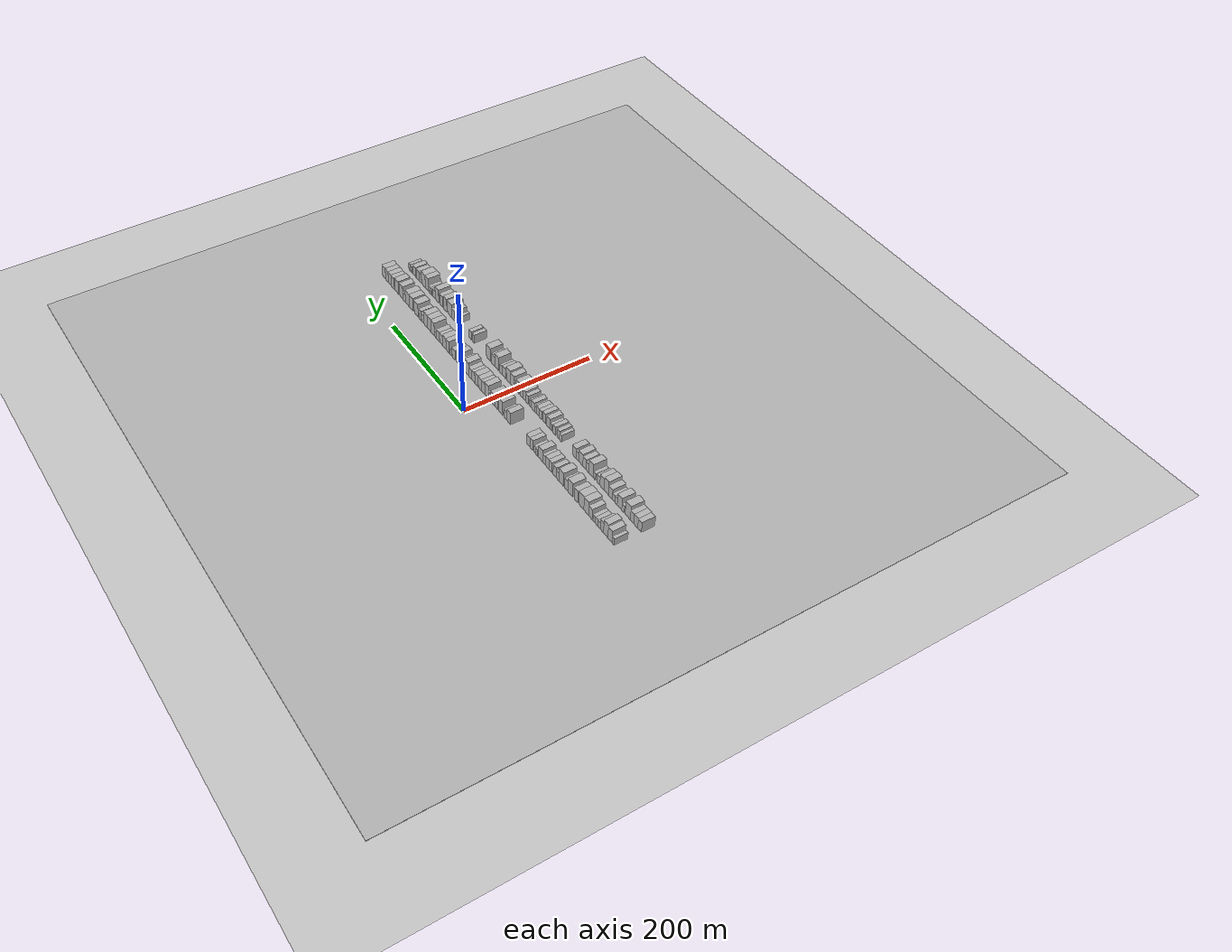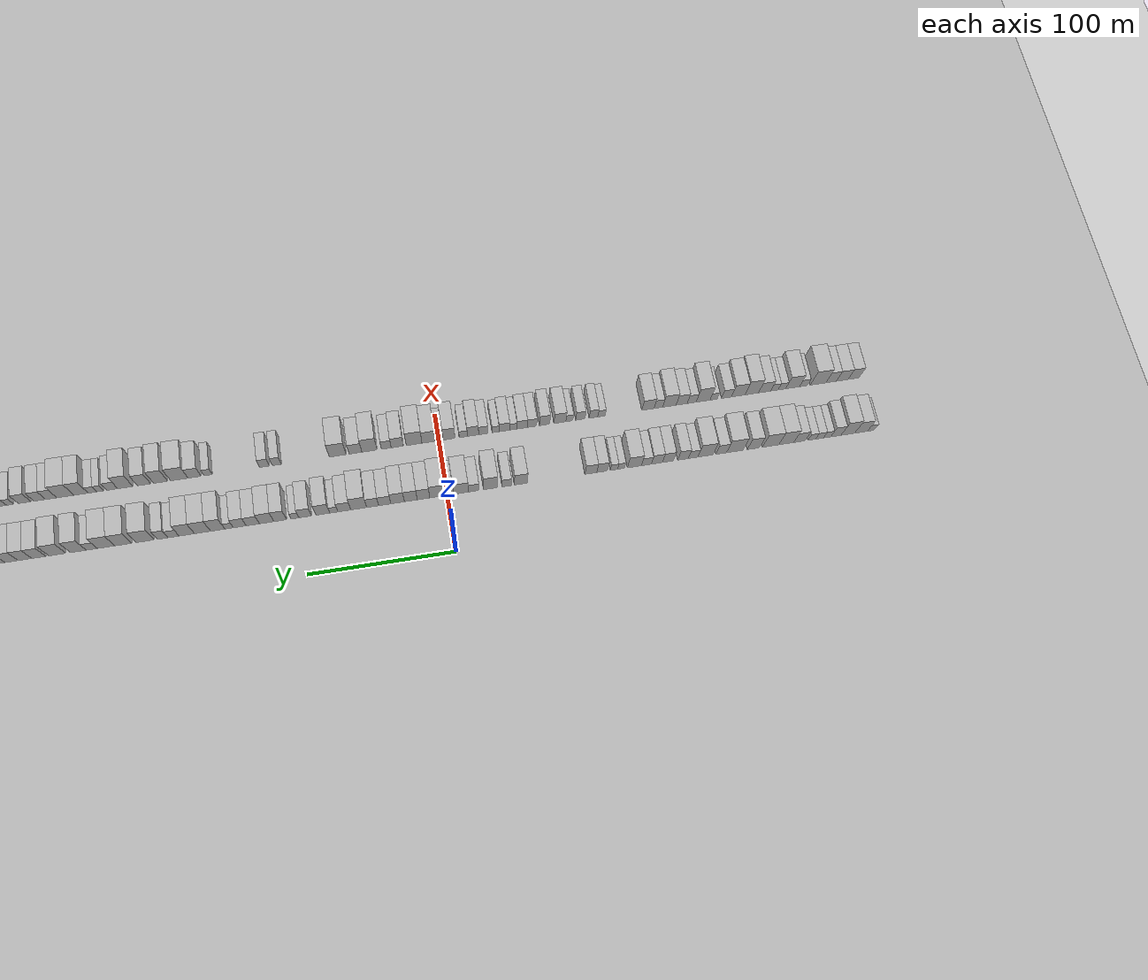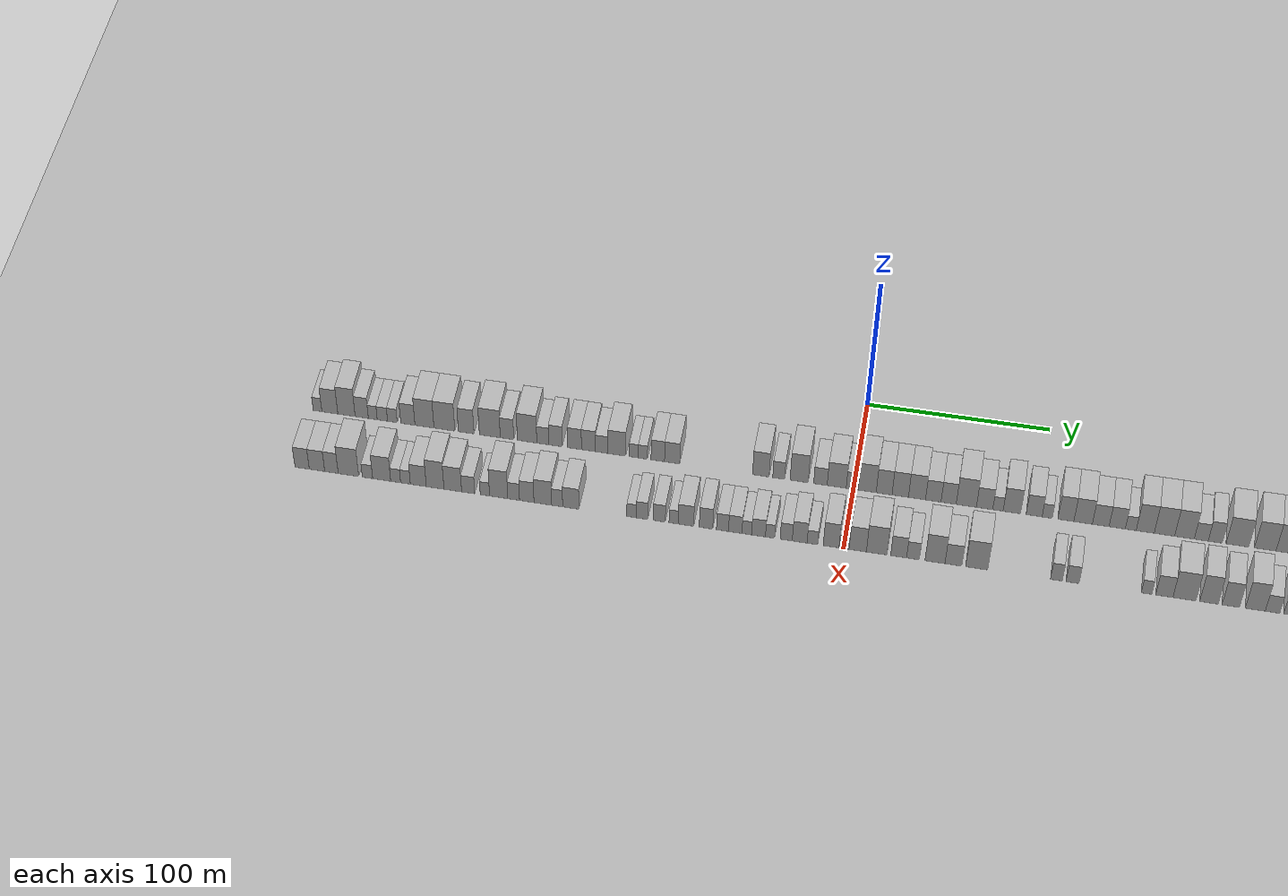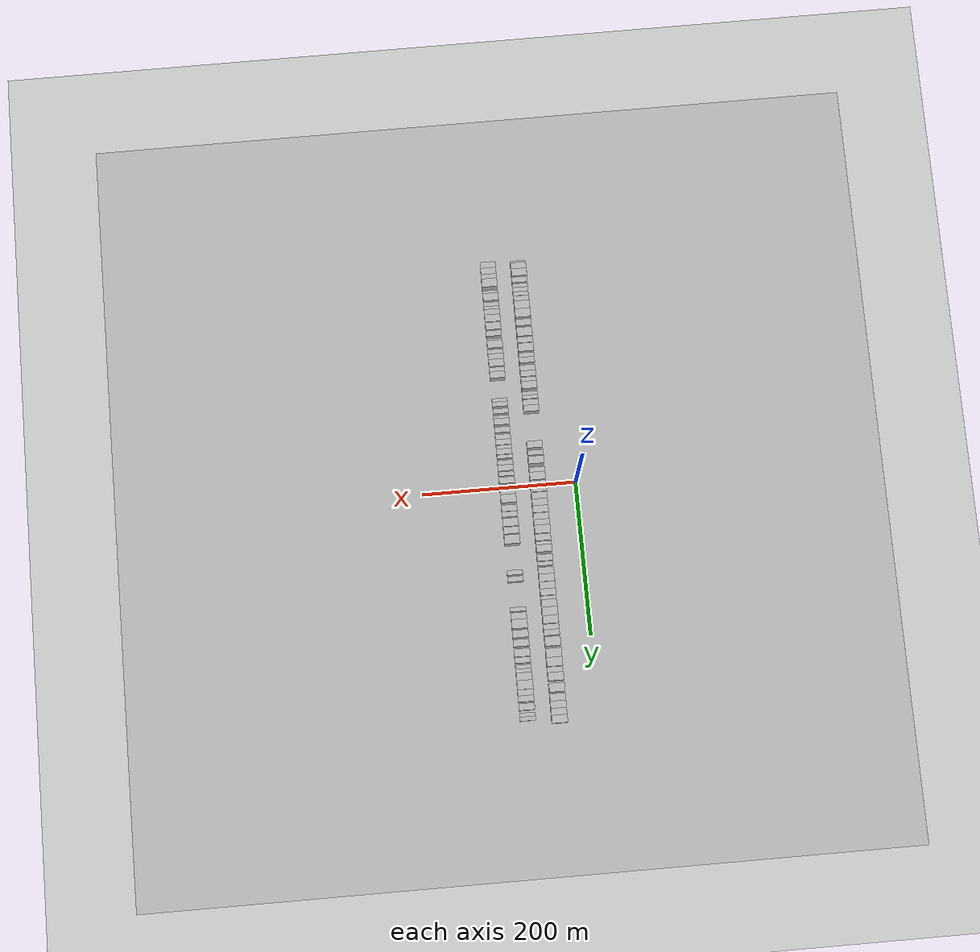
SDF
<?xml version="1.0" encoding="utf-8"?>

<sdf version="1.6">

   <world name="default">

      <gui fullscreen="0">

         <camera name="user_camera">

            <pose>-15 0 4.57585 0 0 0</pose>

            <view_controller>orbit</view_controller>

         </camera>

      </gui>

      <scene>

         <sky>

           <clouds>

             <speed>12</speed>

           </clouds>

         </sky>

         <ambient>0.4 0.4 0.4 1</ambient>

         <background>0.7 0.7 0.7 1</background>

         <shadows>1</shadows>

      </scene>

      <gravity>0 0 -9.8066</gravity>

      <magnetic_field>6e-06 2.3e-05 -4.2e-05</magnetic_field>

      <physics default="0" name="default_physics" type="ode">

         <ode>

            <solver>

               <type>quick</type>

               <iters>10</iters>

               <sor>1.0</sor>

               <use_dynamic_moi_rescaling>0</use_dynamic_moi_rescaling>

            </solver>

            <constraints>

               <cfm>0</cfm>

               <erp>0.2</erp>

               <contact_max_correcting_vel>100</contact_max_correcting_vel>

               <contact_surface_layer>0.001</contact_surface_layer>

            </constraints>

         </ode>

         <max_step_size>0.004</max_step_size>

         <real_time_factor>1</real_time_factor>

         <real_time_update_rate>250</real_time_update_rate>

      </physics>

      <light name="sun" type="directional">

         <cast_shadows>1</cast_shadows>

         <pose>0 0 10 0 0 0</pose>

         <diffuse>0.8 0.8 0.8 1</diffuse>

         <specular>0.2 0.2 0.2 1</specular>

         <attenuation>

            <range>1000</range>

            <constant>0.9</constant>

            <linear>0.01</linear>

            <quadratic>0.001</quadratic>

         </attenuation>

         <direction>-0.5 0.1 -0.9</direction>

      </light>

      <include>

         <name>ground_plane_1</name>

         <uri>model://HANNAS_ground_plane</uri>

         <pose>0 0 0  0 0 0</pose>

      </include>

      <include>

         <name>ground_plane_2</name>

         <uri>model://HANNAS_ground_plane</uri>

         <pose>100 0 0  0 0 0</pose>

      </include>

      <model name="building_1">

         <static>1</static>

         <pose frame="">50.0000 -297.5527 0 0.000000 0.000000 0.000000</pose>

         <link name="link">

            <pose frame="">0 0 6.00 0 0 0</pose>

            <collision name="collision">

               <geometry>

                  <box>

                     <size>20.0000 4.8946 12.0000</size>

                  </box>

               </geometry>

               <max_contacts>10</max_contacts>

               <surface>

                  <contact>

                     <ode/>

                  </contact>

                  <bounce/>

                  <friction>

                     <torsional>

                        <ode/>

                     </torsional>

                     <ode/>

                  </friction>

               </surface>

            </collision>

            <visual name="visual">

               <cast_shadows>0</cast_shadows>

               <geometry>

                  <box>

                     <size>20.0000 4.8946 12.0000</size>

                  </box>

               </geometry>

               <material>

                  <script>

                     <uri>model://HANNAS_wall/materials/scripts</uri>

                     <uri>model://HANNAS_wall/materials/textures</uri>

                     <name>vrc/HANNAS_wall</name>

                  </script>

               </material>

            </visual>

            <self_collide>0</self_collide>

            <enable_wind>0</enable_wind>

            <kinematic>0</kinematic>

         </link>

      </model>

      <model name="building_2">

         <static>1</static>

         <pose frame="">50.0000 -290.5710 0 0.000000 0.000000 0.000000</pose>

         <link name="link">

            <pose frame="">0 0 10.50 0 0 0</pose>

            <collision name="collision">

               <geometry>

                  <box>

                     <size>20.0000 9.0688 21.0000</size>

                  </box>

               </geometry>

               <max_contacts>10</max_contacts>

               <surface>

                  <contact>

                     <ode/>

                  </contact>

                  <bounce/>

                  <friction>

                     <torsional>

                        <ode/>

                     </torsional>

                     <ode/>

                  </friction>

               </surface>

            </collision>

            <visual name="visual">

               <cast_shadows>0</cast_shadows>

               <geometry>

                  <box>

                     <size>20.0000 9.0688 21.0000</size>

                  </box>

               </geometry>

               <material>

                  <script>

                     <uri>model://HANNAS_wall/materials/scripts</uri>

                     <uri>model://HANNAS_wall/materials/textures</uri>

                     <name>vrc/HANNAS_wall</name>

                  </script>

               </material>

            </visual>

            <self_collide>0</self_collide>

            <enable_wind>0</enable_wind>

            <kinematic>0</kinematic>

         </link>

      </model>

      <model name="building_3">

         <static>1</static>

         <pose frame="">50.0000 -281.1410 0 0.000000 0.000000 0.000000</pose>

         <link name="link">

            <pose frame="">0 0 12.00 0 0 0</pose>

            <collision name="collision">

               <geometry>

                  <box>

                     <size>20.0000 9.7911 24.0000</size>

                  </box>

               </geometry>

               <max_contacts>10</max_contacts>

               <surface>

                  <contact>

                     <ode/>

                  </contact>

                  <bounce/>

                  <friction>

                     <torsional>

                        <ode/>

                     </torsional>

                     <ode/>

                  </friction>

               </surface>

            </collision>

            <visual name="visual">

               <cast_shadows>0</cast_shadows>

               <geometry>

                  <box>

                     <size>20.0000 9.7911 24.0000</size>

                  </box>

               </geometry>

               <material>

                  <script>

                     <uri>model://HANNAS_wall/materials/scripts</uri>

                     <uri>model://HANNAS_wall/materials/textures</uri>

                     <name>vrc/HANNAS_wall</name>

                  </script>

               </material>

            </visual>

            <self_collide>0</self_collide>

            <enable_wind>0</enable_wind>

            <kinematic>0</kinematic>

         </link>

      </model>

      <model name="building_4">

         <static>1</static>

         <pose frame="">50.0000 -272.5372 0 0.000000 0.000000 0.000000</pose>

         <link name="link">

            <pose frame="">0 0 9.00 0 0 0</pose>

            <collision name="collision">

               <geometry>

                  <box>

                     <size>20.0000 7.4165 18.0000</size>

                  </box>

               </geometry>

               <max_contacts>10</max_contacts>

               <surface>

                  <contact>

                     <ode/>

                  </contact>

                  <bounce/>

                  <friction>

                     <torsional>

                        <ode/>

                     </torsional>

                     <ode/>

                  </friction>

               </surface>

            </collision>

            <visual name="visual">

               <cast_shadows>0</cast_shadows>

               <geometry>

                  <box>

                     <size>20.0000 7.4165 18.0000</size>

                  </box>

               </geometry>

               <material>

                  <script>

                     <uri>model://HANNAS_wall/materials/scripts</uri>

                     <uri>model://HANNAS_wall/materials/textures</uri>

                     <name>vrc/HANNAS_wall</name>

                  </script>

               </material>

            </visual>

            <self_collide>0</self_collide>

            <enable_wind>0</enable_wind>

            <kinematic>0</kinematic>

         </link>

      </model>

      <model name="building_5">

         <static>1</static>

         <pose frame="">50.0000 -266.3257 0 0.000000 0.000000 0.000000</pose>

         <link name="link">

            <pose frame="">0 0 6.00 0 0 0</pose>

            <collision name="collision">

               <geometry>

                  <box>

                     <size>20.0000 5.0066 12.0000</size>

                  </box>

               </geometry>

               <max_contacts>10</max_contacts>

               <surface>

                  <contact>

                     <ode/>

                  </contact>

                  <bounce/>

                  <friction>

                     <torsional>

                        <ode/>

                     </torsional>

                     <ode/>

                  </friction>

               </surface>

            </collision>

            <visual name="visual">

               <cast_shadows>0</cast_shadows>

               <geometry>

                  <box>

                     <size>20.0000 5.0066 12.0000</size>

                  </box>

               </geometry>

               <material>

                  <script>

                     <uri>model://HANNAS_wall/materials/scripts</uri>

                     <uri>model://HANNAS_wall/materials/textures</uri>

                     <name>vrc/HANNAS_wall</name>

                  </script>

               </material>

            </visual>

            <self_collide>0</self_collide>

            <enable_wind>0</enable_wind>

            <kinematic>0</kinematic>

         </link>

      </model>

      <model name="building_6">

         <static>1</static>

         <pose frame="">50.0000 -260.9145 0 0.000000 0.000000 0.000000</pose>

         <link name="link">

            <pose frame="">0 0 6.00 0 0 0</pose>

            <collision name="collision">

               <geometry>

                  <box>

                     <size>20.0000 5.8157 12.0000</size>

                  </box>

               </geometry>

               <max_contacts>10</max_contacts>

               <surface>

                  <contact>

                     <ode/>

                  </contact>

                  <bounce/>

                  <friction>

                     <torsional>

                        <ode/>

                     </torsional>

                     <ode/>

                  </friction>

               </surface>

            </collision>

            <visual name="visual">

               <cast_shadows>0</cast_shadows>

               <geometry>

                  <box>

                     <size>20.0000 5.8157 12.0000</size>

                  </box>

               </geometry>

               <material>

                  <script>

                     <uri>model://HANNAS_wall/materials/scripts</uri>

                     <uri>model://HANNAS_wall/materials/textures</uri>

                     <name>vrc/HANNAS_wall</name>

                  </script>

               </material>

            </visual>

            <self_collide>0</self_collide>

            <enable_wind>0</enable_wind>

            <kinematic>0</kinematic>

         </link>

      </model>

      <model name="building_7">

         <static>1</static>

         <pose frame="">50.0000 -255.2807 0 0.000000 0.000000 0.000000</pose>

         <link name="link">

            <pose frame="">0 0 6.00 0 0 0</pose>

            <collision name="collision">

               <geometry>

                  <box>

                     <size>20.0000 5.4520 12.0000</size>

                  </box>

               </geometry>

               <max_contacts>10</max_contacts>

               <surface>

                  <contact>

                     <ode/>

                  </contact>

                  <bounce/>

                  <friction>

                     <torsional>

                        <ode/>

                     </torsional>

                     <ode/>

                  </friction>

               </surface>

            </collision>

            <visual name="visual">

               <cast_shadows>0</cast_shadows>

               <geometry>

                  <box>

                     <size>20.0000 5.4520 12.0000</size>

                  </box>

               </geometry>

               <material>

                  <script>

                     <uri>model://HANNAS_wall/materials/scripts</uri>

                     <uri>model://HANNAS_wall/materials/textures</uri>

                     <name>vrc/HANNAS_wall</name>

                  </script>

               </material>

            </visual>

            <self_collide>0</self_collide>

            <enable_wind>0</enable_wind>

            <kinematic>0</kinematic>

         </link>

      </model>

      <model name="building_8">

         <static>1</static>

         <pose frame="">50.0000 -246.5573 0 0.000000 0.000000 0.000000</pose>

         <link name="link">

            <pose frame="">0 0 9.00 0 0 0</pose>

            <collision name="collision">

               <geometry>

                  <box>

                     <size>20.0000 7.9948 18.0000</size>

                  </box>

               </geometry>

               <max_contacts>10</max_contacts>

               <surface>

                  <contact>

                     <ode/>

                  </contact>

                  <bounce/>

                  <friction>

                     <torsional>

                        <ode/>

                     </torsional>

                     <ode/>

                  </friction>

               </surface>

            </collision>

            <visual name="visual">

               <cast_shadows>0</cast_shadows>

               <geometry>

                  <box>

                     <size>20.0000 7.9948 18.0000</size>

                  </box>

               </geometry>

               <material>

                  <script>

                     <uri>model://HANNAS_wall/materials/scripts</uri>

                     <uri>model://HANNAS_wall/materials/textures</uri>

                     <name>vrc/HANNAS_wall</name>

                  </script>

               </material>

            </visual>

            <self_collide>0</self_collide>

            <enable_wind>0</enable_wind>

            <kinematic>0</kinematic>

         </link>

      </model>

      <model name="building_9">

         <static>1</static>

         <pose frame="">50.0000 -237.2130 0 0.000000 0.000000 0.000000</pose>

         <link name="link">

            <pose frame="">0 0 12.00 0 0 0</pose>

            <collision name="collision">

               <geometry>

                  <box>

                     <size>20.0000 10.6939 24.0000</size>

                  </box>

               </geometry>

               <max_contacts>10</max_contacts>

               <surface>

                  <contact>

                     <ode/>

                  </contact>

                  <bounce/>

                  <friction>

                     <torsional>

                        <ode/>

                     </torsional>

                     <ode/>

                  </friction>

               </surface>

            </collision>

            <visual name="visual">

               <cast_shadows>0</cast_shadows>

               <geometry>

                  <box>

                     <size>20.0000 10.6939 24.0000</size>

                  </box>

               </geometry>

               <material>

                  <script>

                     <uri>model://HANNAS_wall/materials/scripts</uri>

                     <uri>model://HANNAS_wall/materials/textures</uri>

                     <name>vrc/HANNAS_wall</name>

                  </script>

               </material>

            </visual>

            <self_collide>0</self_collide>

            <enable_wind>0</enable_wind>

            <kinematic>0</kinematic>

         </link>

      </model>

      <model name="building_10">

         <static>1</static>

         <pose frame="">50.0000 -226.0155 0 0.000000 0.000000 0.000000</pose>

         <link name="link">

            <pose frame="">0 0 12.00 0 0 0</pose>

            <collision name="collision">

               <geometry>

                  <box>

                     <size>20.0000 11.7012 24.0000</size>

                  </box>

               </geometry>

               <max_contacts>10</max_contacts>

               <surface>

                  <contact>

                     <ode/>

                  </contact>

                  <bounce/>

                  <friction>

                     <torsional>

                        <ode/>

                     </torsional>

                     <ode/>

                  </friction>

               </surface>

            </collision>

            <visual name="visual">

               <cast_shadows>0</cast_shadows>

               <geometry>

                  <box>

                     <size>20.0000 11.7012 24.0000</size>

                  </box>

               </geometry>

               <material>

                  <script>

                     <uri>model://HANNAS_wall/materials/scripts</uri>

                     <uri>model://HANNAS_wall/materials/textures</uri>

                     <name>vrc/HANNAS_wall</name>

                  </script>

               </material>

            </visual>

            <self_collide>0</self_collide>

            <enable_wind>0</enable_wind>

            <kinematic>0</kinematic>

         </link>

      </model>

      <model name="building_11">

         <static>1</static>

         <pose frame="">50.0000 -213.7931 0 0.000000 0.000000 0.000000</pose>

         <link name="link">

            <pose frame="">0 0 10.50 0 0 0</pose>

            <collision name="collision">

               <geometry>

                  <box>

                     <size>20.0000 8.7436 21.0000</size>

                  </box>

               </geometry>

               <max_contacts>10</max_contacts>

               <surface>

                  <contact>

                     <ode/>

                  </contact>

                  <bounce/>

                  <friction>

                     <torsional>

                        <ode/>

                     </torsional>

                     <ode/>

                  </friction>

               </surface>

            </collision>

            <visual name="visual">

               <cast_shadows>0</cast_shadows>

               <geometry>

                  <box>

                     <size>20.0000 8.7436 21.0000</size>

                  </box>

               </geometry>

               <material>

                  <script>

                     <uri>model://HANNAS_wall/materials/scripts</uri>

                     <uri>model://HANNAS_wall/materials/textures</uri>

                     <name>vrc/HANNAS_wall</name>

                  </script>

               </material>

            </visual>

            <self_collide>0</self_collide>

            <enable_wind>0</enable_wind>

            <kinematic>0</kinematic>

         </link>

      </model>

      <model name="building_12">

         <static>1</static>

         <pose frame="">50.0000 -200.5853 0 0.000000 0.000000 0.000000</pose>

         <link name="link">

            <pose frame="">0 0 12.00 0 0 0</pose>

            <collision name="collision">

               <geometry>

                  <box>

                     <size>20.0000 11.6719 24.0000</size>

                  </box>

               </geometry>

               <max_contacts>10</max_contacts>

               <surface>

                  <contact>

                     <ode/>

                  </contact>

                  <bounce/>

                  <friction>

                     <torsional>

                        <ode/>

                     </torsional>

                     <ode/>

                  </friction>

               </surface>

            </collision>

            <visual name="visual">

               <cast_shadows>0</cast_shadows>

               <geometry>

                  <box>

                     <size>20.0000 11.6719 24.0000</size>

                  </box>

               </geometry>

               <material>

                  <script>

                     <uri>model://HANNAS_wall/materials/scripts</uri>

                     <uri>model://HANNAS_wall/materials/textures</uri>

                     <name>vrc/HANNAS_wall</name>

                  </script>

               </material>

            </visual>

            <self_collide>0</self_collide>

            <enable_wind>0</enable_wind>

            <kinematic>0</kinematic>

         </link>

      </model>

      <model name="building_13">

         <static>1</static>

         <pose frame="">50.0000 -190.9823 0 0.000000 0.000000 0.000000</pose>

         <link name="link">

            <pose frame="">0 0 9.00 0 0 0</pose>

            <collision name="collision">

               <geometry>

                  <box>

                     <size>20.0000 7.5342 18.0000</size>

                  </box>

               </geometry>

               <max_contacts>10</max_contacts>

               <surface>

                  <contact>

                     <ode/>

                  </contact>

                  <bounce/>

                  <friction>

                     <torsional>

                        <ode/>

                     </torsional>

                     <ode/>

                  </friction>

               </surface>

            </collision>

            <visual name="visual">

               <cast_shadows>0</cast_shadows>

               <geometry>

                  <box>

                     <size>20.0000 7.5342 18.0000</size>

                  </box>

               </geometry>

               <material>

                  <script>

                     <uri>model://HANNAS_wall/materials/scripts</uri>

                     <uri>model://HANNAS_wall/materials/textures</uri>

                     <name>vrc/HANNAS_wall</name>

                  </script>

               </material>

            </visual>

            <self_collide>0</self_collide>

            <enable_wind>0</enable_wind>

            <kinematic>0</kinematic>

         </link>

      </model>

      <model name="building_14">

         <static>1</static>

         <pose frame="">50.0000 -179.7867 0 0.000000 0.000000 0.000000</pose>

         <link name="link">

            <pose frame="">0 0 12.00 0 0 0</pose>

            <collision name="collision">

               <geometry>

                  <box>

                     <size>20.0000 10.8569 24.0000</size>

                  </box>

               </geometry>

               <max_contacts>10</max_contacts>

               <surface>

                  <contact>

                     <ode/>

                  </contact>

                  <bounce/>

                  <friction>

                     <torsional>

                        <ode/>

                     </torsional>

                     <ode/>

                  </friction>

               </surface>

            </collision>

            <visual name="visual">

               <cast_shadows>0</cast_shadows>

               <geometry>

                  <box>

                     <size>20.0000 10.8569 24.0000</size>

                  </box>

               </geometry>

               <material>

                  <script>

                     <uri>model://HANNAS_wall/materials/scripts</uri>

                     <uri>model://HANNAS_wall/materials/textures</uri>

                     <name>vrc/HANNAS_wall</name>

                  </script>

               </material>

            </visual>

            <self_collide>0</self_collide>

            <enable_wind>0</enable_wind>

            <kinematic>0</kinematic>

         </link>

      </model>

      <model name="building_15">

         <static>1</static>

         <pose frame="">50.0000 -171.0333 0 0.000000 0.000000 0.000000</pose>

         <link name="link">

            <pose frame="">0 0 7.50 0 0 0</pose>

            <collision name="collision">

               <geometry>

                  <box>

                     <size>20.0000 6.6499 15.0000</size>

                  </box>

               </geometry>

               <max_contacts>10</max_contacts>

               <surface>

                  <contact>

                     <ode/>

                  </contact>

                  <bounce/>

                  <friction>

                     <torsional>

                        <ode/>

                     </torsional>

                     <ode/>

                  </friction>

               </surface>

            </collision>

            <visual name="visual">

               <cast_shadows>0</cast_shadows>

               <geometry>

                  <box>

                     <size>20.0000 6.6499 15.0000</size>

                  </box>

               </geometry>

               <material>

                  <script>

                     <uri>model://HANNAS_wall/materials/scripts</uri>

                     <uri>model://HANNAS_wall/materials/textures</uri>

                     <name>vrc/HANNAS_wall</name>

                  </script>

               </material>

            </visual>

            <self_collide>0</self_collide>

            <enable_wind>0</enable_wind>

            <kinematic>0</kinematic>

         </link>

      </model>

      <model name="building_16">

         <static>1</static>

         <pose frame="">50.0000 -163.9777 0 0.000000 0.000000 0.000000</pose>

         <link name="link">

            <pose frame="">0 0 9.00 0 0 0</pose>

            <collision name="collision">

               <geometry>

                  <box>

                     <size>20.0000 7.4614 18.0000</size>

                  </box>

               </geometry>

               <max_contacts>10</max_contacts>

               <surface>

                  <contact>

                     <ode/>

                  </contact>

                  <bounce/>

                  <friction>

                     <torsional>

                        <ode/>

                     </torsional>

                     <ode/>

                  </friction>

               </surface>

            </collision>

            <visual name="visual">

               <cast_shadows>0</cast_shadows>

               <geometry>

                  <box>

                     <size>20.0000 7.4614 18.0000</size>

                  </box>

               </geometry>

               <material>

                  <script>

                     <uri>model://HANNAS_wall/materials/scripts</uri>

                     <uri>model://HANNAS_wall/materials/textures</uri>

                     <name>vrc/HANNAS_wall</name>

                  </script>

               </material>

            </visual>

            <self_collide>0</self_collide>

            <enable_wind>0</enable_wind>

            <kinematic>0</kinematic>

         </link>

      </model>

      <model name="building_17">

         <static>1</static>

         <pose frame="">50.0000 -153.3974 0 0.000000 0.000000 0.000000</pose>

         <link name="link">

            <pose frame="">0 0 9.00 0 0 0</pose>

            <collision name="collision">

               <geometry>

                  <box>

                     <size>20.0000 7.6990 18.0000</size>

                  </box>

               </geometry>

               <max_contacts>10</max_contacts>

               <surface>

                  <contact>

                     <ode/>

                  </contact>

                  <bounce/>

                  <friction>

                     <torsional>

                        <ode/>

                     </torsional>

                     <ode/>

                  </friction>

               </surface>

            </collision>

            <visual name="visual">

               <cast_shadows>0</cast_shadows>

               <geometry>

                  <box>

                     <size>20.0000 7.6990 18.0000</size>

                  </box>

               </geometry>

               <material>

                  <script>

                     <uri>model://HANNAS_wall/materials/scripts</uri>

                     <uri>model://HANNAS_wall/materials/textures</uri>

                     <name>vrc/HANNAS_wall</name>

                  </script>

               </material>

            </visual>

            <self_collide>0</self_collide>

            <enable_wind>0</enable_wind>

            <kinematic>0</kinematic>

         </link>

      </model>

      <model name="building_18">

         <static>1</static>

         <pose frame="">50.0000 -145.6617 0 0.000000 0.000000 0.000000</pose>

         <link name="link">

            <pose frame="">0 0 9.00 0 0 0</pose>

            <collision name="collision">

               <geometry>

                  <box>

                     <size>20.0000 7.7725 18.0000</size>

                  </box>

               </geometry>

               <max_contacts>10</max_contacts>

               <surface>

                  <contact>

                     <ode/>

                  </contact>

                  <bounce/>

                  <friction>

                     <torsional>

                        <ode/>

                     </torsional>

                     <ode/>

                  </friction>

               </surface>

            </collision>

            <visual name="visual">

               <cast_shadows>0</cast_shadows>

               <geometry>

                  <box>

                     <size>20.0000 7.7725 18.0000</size>

                  </box>

               </geometry>

               <material>

                  <script>

                     <uri>model://HANNAS_wall/materials/scripts</uri>

                     <uri>model://HANNAS_wall/materials/textures</uri>

                     <name>vrc/HANNAS_wall</name>

                  </script>

               </material>

            </visual>

            <self_collide>0</self_collide>

            <enable_wind>0</enable_wind>

            <kinematic>0</kinematic>

         </link>

      </model>

      <model name="building_19">

         <static>1</static>

         <pose frame="">50.0000 -138.2961 0 0.000000 0.000000 0.000000</pose>

         <link name="link">

            <pose frame="">0 0 7.50 0 0 0</pose>

            <collision name="collision">

               <geometry>

                  <box>

                     <size>20.0000 6.9588 15.0000</size>

                  </box>

               </geometry>

               <max_contacts>10</max_contacts>

               <surface>

                  <contact>

                     <ode/>

                  </contact>

                  <bounce/>

                  <friction>

                     <torsional>

                        <ode/>

                     </torsional>

                     <ode/>

                  </friction>

               </surface>

            </collision>

            <visual name="visual">

               <cast_shadows>0</cast_shadows>

               <geometry>

                  <box>

                     <size>20.0000 6.9588 15.0000</size>

                  </box>

               </geometry>

               <material>

                  <script>

                     <uri>model://HANNAS_wall/materials/scripts</uri>

                     <uri>model://HANNAS_wall/materials/textures</uri>

                     <name>vrc/HANNAS_wall</name>

                  </script>

               </material>

            </visual>

            <self_collide>0</self_collide>

            <enable_wind>0</enable_wind>

            <kinematic>0</kinematic>

         </link>

      </model>

      <model name="building_20">

         <static>1</static>

         <pose frame="">50.0000 -129.9064 0 0.000000 0.000000 0.000000</pose>

         <link name="link">

            <pose frame="">0 0 10.50 0 0 0</pose>

            <collision name="collision">

               <geometry>

                  <box>

                     <size>20.0000 9.8205 21.0000</size>

                  </box>

               </geometry>

               <max_contacts>10</max_contacts>

               <surface>

                  <contact>

                     <ode/>

                  </contact>

                  <bounce/>

                  <friction>

                     <torsional>

                        <ode/>

                     </torsional>

                     <ode/>

                  </friction>

               </surface>

            </collision>

            <visual name="visual">

               <cast_shadows>0</cast_shadows>

               <geometry>

                  <box>

                     <size>20.0000 9.8205 21.0000</size>

                  </box>

               </geometry>

               <material>

                  <script>

                     <uri>model://HANNAS_wall/materials/scripts</uri>

                     <uri>model://HANNAS_wall/materials/textures</uri>

                     <name>vrc/HANNAS_wall</name>

                  </script>

               </material>

            </visual>

            <self_collide>0</self_collide>

            <enable_wind>0</enable_wind>

            <kinematic>0</kinematic>

         </link>

      </model>

      <model name="building_21">

         <static>1</static>

         <pose frame="">50.0000 -120.5485 0 0.000000 0.000000 0.000000</pose>

         <link name="link">

            <pose frame="">0 0 6.00 0 0 0</pose>

            <collision name="collision">

               <geometry>

                  <box>

                     <size>20.0000 4.8953 12.0000</size>

                  </box>

               </geometry>

               <max_contacts>10</max_contacts>

               <surface>

                  <contact>

                     <ode/>

                  </contact>

                  <bounce/>

                  <friction>

                     <torsional>

                        <ode/>

                     </torsional>

                     <ode/>

                  </friction>

               </surface>

            </collision>

            <visual name="visual">

               <cast_shadows>0</cast_shadows>

               <geometry>

                  <box>

                     <size>20.0000 4.8953 12.0000</size>

                  </box>

               </geometry>

               <material>

                  <script>

                     <uri>model://HANNAS_wall/materials/scripts</uri>

                     <uri>model://HANNAS_wall/materials/textures</uri>

                     <name>vrc/HANNAS_wall</name>

                  </script>

               </material>

            </visual>

            <self_collide>0</self_collide>

            <enable_wind>0</enable_wind>

            <kinematic>0</kinematic>

         </link>

      </model>

      <model name="building_22">

         <static>1</static>

         <pose frame="">50.0000 -115.5680 0 0.000000 0.000000 0.000000</pose>

         <link name="link">

            <pose frame="">0 0 6.00 0 0 0</pose>

            <collision name="collision">

               <geometry>

                  <box>

                     <size>20.0000 5.0657 12.0000</size>

                  </box>

               </geometry>

               <max_contacts>10</max_contacts>

               <surface>

                  <contact>

                     <ode/>

                  </contact>

                  <bounce/>

                  <friction>

                     <torsional>

                        <ode/>

                     </torsional>

                     <ode/>

                  </friction>

               </surface>

            </collision>

            <visual name="visual">

               <cast_shadows>0</cast_shadows>

               <geometry>

                  <box>

                     <size>20.0000 5.0657 12.0000</size>

                  </box>

               </geometry>

               <material>

                  <script>

                     <uri>model://HANNAS_wall/materials/scripts</uri>

                     <uri>model://HANNAS_wall/materials/textures</uri>

                     <name>vrc/HANNAS_wall</name>

                  </script>

               </material>

            </visual>

            <self_collide>0</self_collide>

            <enable_wind>0</enable_wind>

            <kinematic>0</kinematic>

         </link>

      </model>

      <model name="building_23">

         <static>1</static>

         <pose frame="">50.0000 -107.3214 0 0.000000 0.000000 0.000000</pose>

         <link name="link">

            <pose frame="">0 0 9.00 0 0 0</pose>

            <collision name="collision">

               <geometry>

                  <box>

                     <size>20.0000 7.4274 18.0000</size>

                  </box>

               </geometry>

               <max_contacts>10</max_contacts>

               <surface>

                  <contact>

                     <ode/>

                  </contact>

                  <bounce/>

                  <friction>

                     <torsional>

                        <ode/>

                     </torsional>

                     <ode/>

                  </friction>

               </surface>

            </collision>

            <visual name="visual">

               <cast_shadows>0</cast_shadows>

               <geometry>

                  <box>

                     <size>20.0000 7.4274 18.0000</size>

                  </box>

               </geometry>

               <material>

                  <script>

                     <uri>model://HANNAS_wall/materials/scripts</uri>

                     <uri>model://HANNAS_wall/materials/textures</uri>

                     <name>vrc/HANNAS_wall</name>

                  </script>

               </material>

            </visual>

            <self_collide>0</self_collide>

            <enable_wind>0</enable_wind>

            <kinematic>0</kinematic>

         </link>

      </model>

      <model name="building_24">

         <static>1</static>

         <pose frame="">50.0000 -99.4239 0 0.000000 0.000000 0.000000</pose>

         <link name="link">

            <pose frame="">0 0 9.00 0 0 0</pose>

            <collision name="collision">

               <geometry>

                  <box>

                     <size>20.0000 8.3677 18.0000</size>

                  </box>

               </geometry>

               <max_contacts>10</max_contacts>

               <surface>

                  <contact>

                     <ode/>

                  </contact>

                  <bounce/>

                  <friction>

                     <torsional>

                        <ode/>

                     </torsional>

                     <ode/>

                  </friction>

               </surface>

            </collision>

            <visual name="visual">

               <cast_shadows>0</cast_shadows>

               <geometry>

                  <box>

                     <size>20.0000 8.3677 18.0000</size>

                  </box>

               </geometry>

               <material>

                  <script>

                     <uri>model://HANNAS_wall/materials/scripts</uri>

                     <uri>model://HANNAS_wall/materials/textures</uri>

                     <name>vrc/HANNAS_wall</name>

                  </script>

               </material>

            </visual>

            <self_collide>0</self_collide>

            <enable_wind>0</enable_wind>

            <kinematic>0</kinematic>

         </link>

      </model>

      <model name="building_25">

         <static>1</static>

         <pose frame="">50.0000 -50.7242 0 0.000000 0.000000 0.000000</pose>

         <link name="link">

            <pose frame="">0 0 10.50 0 0 0</pose>

            <collision name="collision">

               <geometry>

                  <box>

                     <size>20.0000 9.0105 21.0000</size>

                  </box>

               </geometry>

               <max_contacts>10</max_contacts>

               <surface>

                  <contact>

                     <ode/>

                  </contact>

                  <bounce/>

                  <friction>

                     <torsional>

                        <ode/>

                     </torsional>

                     <ode/>

                  </friction>

               </surface>

            </collision>

            <visual name="visual">

               <cast_shadows>0</cast_shadows>

               <geometry>

                  <box>

                     <size>20.0000 9.0105 21.0000</size>

                  </box>

               </geometry>

               <material>

                  <script>

                     <uri>model://HANNAS_wall/materials/scripts</uri>

                     <uri>model://HANNAS_wall/materials/textures</uri>

                     <name>vrc/HANNAS_wall</name>

                  </script>

               </material>

            </visual>

            <self_collide>0</self_collide>

            <enable_wind>0</enable_wind>

            <kinematic>0</kinematic>

         </link>

      </model>

      <model name="building_26">

         <static>1</static>

         <pose frame="">50.0000 -40.9779 0 0.000000 0.000000 0.000000</pose>

         <link name="link">

            <pose frame="">0 0 7.50 0 0 0</pose>

            <collision name="collision">

               <geometry>

                  <box>

                     <size>20.0000 6.4822 15.0000</size>

                  </box>

               </geometry>

               <max_contacts>10</max_contacts>

               <surface>

                  <contact>

                     <ode/>

                  </contact>

                  <bounce/>

                  <friction>

                     <torsional>

                        <ode/>

                     </torsional>

                     <ode/>

                  </friction>

               </surface>

            </collision>

            <visual name="visual">

               <cast_shadows>0</cast_shadows>

               <geometry>

                  <box>

                     <size>20.0000 6.4822 15.0000</size>

                  </box>

               </geometry>

               <material>

                  <script>

                     <uri>model://HANNAS_wall/materials/scripts</uri>

                     <uri>model://HANNAS_wall/materials/textures</uri>

                     <name>vrc/HANNAS_wall</name>

                  </script>

               </material>

            </visual>

            <self_collide>0</self_collide>

            <enable_wind>0</enable_wind>

            <kinematic>0</kinematic>

         </link>

      </model>

      <model name="building_27">

         <static>1</static>

         <pose frame="">50.0000 -29.8061 0 0.000000 0.000000 0.000000</pose>

         <link name="link">

            <pose frame="">0 0 12.00 0 0 0</pose>

            <collision name="collision">

               <geometry>

                  <box>

                     <size>20.0000 9.8613 24.0000</size>

                  </box>

               </geometry>

               <max_contacts>10</max_contacts>

               <surface>

                  <contact>

                     <ode/>

                  </contact>

                  <bounce/>

                  <friction>

                     <torsional>

                        <ode/>

                     </torsional>

                     <ode/>

                  </friction>

               </surface>

            </collision>

            <visual name="visual">

               <cast_shadows>0</cast_shadows>

               <geometry>

                  <box>

                     <size>20.0000 9.8613 24.0000</size>

                  </box>

               </geometry>

               <material>

                  <script>

                     <uri>model://HANNAS_wall/materials/scripts</uri>

                     <uri>model://HANNAS_wall/materials/textures</uri>

                     <name>vrc/HANNAS_wall</name>

                  </script>

               </material>

            </visual>

            <self_collide>0</self_collide>

            <enable_wind>0</enable_wind>

            <kinematic>0</kinematic>

         </link>

      </model>

      <model name="building_28">

         <static>1</static>

         <pose frame="">50.0000 -18.1943 0 0.000000 0.000000 0.000000</pose>

         <link name="link">

            <pose frame="">0 0 7.50 0 0 0</pose>

            <collision name="collision">

               <geometry>

                  <box>

                     <size>20.0000 7.3623 15.0000</size>

                  </box>

               </geometry>

               <max_contacts>10</max_contacts>

               <surface>

                  <contact>

                     <ode/>

                  </contact>

                  <bounce/>

                  <friction>

                     <torsional>

                        <ode/>

                     </torsional>

                     <ode/>

                  </friction>

               </surface>

            </collision>

            <visual name="visual">

               <cast_shadows>0</cast_shadows>

               <geometry>

                  <box>

                     <size>20.0000 7.3623 15.0000</size>

                  </box>

               </geometry>

               <material>

                  <script>

                     <uri>model://HANNAS_wall/materials/scripts</uri>

                     <uri>model://HANNAS_wall/materials/textures</uri>

                     <name>vrc/HANNAS_wall</name>

                  </script>

               </material>

            </visual>

            <self_collide>0</self_collide>

            <enable_wind>0</enable_wind>

            <kinematic>0</kinematic>

         </link>

      </model>

      <model name="building_29">

         <static>1</static>

         <pose frame="">50.0000 -9.3427 0 0.000000 0.000000 0.000000</pose>

         <link name="link">

            <pose frame="">0 0 10.50 0 0 0</pose>

            <collision name="collision">

               <geometry>

                  <box>

                     <size>20.0000 10.3411 21.0000</size>

                  </box>

               </geometry>

               <max_contacts>10</max_contacts>

               <surface>

                  <contact>

                     <ode/>

                  </contact>

                  <bounce/>

                  <friction>

                     <torsional>

                        <ode/>

                     </torsional>

                     <ode/>

                  </friction>

               </surface>

            </collision>

            <visual name="visual">

               <cast_shadows>0</cast_shadows>

               <geometry>

                  <box>

                     <size>20.0000 10.3411 21.0000</size>

                  </box>

               </geometry>

               <material>

                  <script>

                     <uri>model://HANNAS_wall/materials/scripts</uri>

                     <uri>model://HANNAS_wall/materials/textures</uri>

                     <name>vrc/HANNAS_wall</name>

                  </script>

               </material>

            </visual>

            <self_collide>0</self_collide>

            <enable_wind>0</enable_wind>

            <kinematic>0</kinematic>

         </link>

      </model>

      <model name="building_30">

         <static>1</static>

         <pose frame="">50.0000 -0.9263 0 0.000000 0.000000 0.000000</pose>

         <link name="link">

            <pose frame="">0 0 7.50 0 0 0</pose>

            <collision name="collision">

               <geometry>

                  <box>

                     <size>20.0000 6.4915 15.0000</size>

                  </box>

               </geometry>

               <max_contacts>10</max_contacts>

               <surface>

                  <contact>

                     <ode/>

                  </contact>

                  <bounce/>

                  <friction>

                     <torsional>

                        <ode/>

                     </torsional>

                     <ode/>

                  </friction>

               </surface>

            </collision>

            <visual name="visual">

               <cast_shadows>0</cast_shadows>

               <geometry>

                  <box>

                     <size>20.0000 6.4915 15.0000</size>

                  </box>

               </geometry>

               <material>

                  <script>

                     <uri>model://HANNAS_wall/materials/scripts</uri>

                     <uri>model://HANNAS_wall/materials/textures</uri>

                     <name>vrc/HANNAS_wall</name>

                  </script>

               </material>

            </visual>

            <self_collide>0</self_collide>

            <enable_wind>0</enable_wind>

            <kinematic>0</kinematic>

         </link>

      </model>

      <model name="building_31">

         <static>1</static>

         <pose frame="">50.0000 7.2069 0 0.000000 0.000000 0.000000</pose>

         <link name="link">

            <pose frame="">0 0 12.00 0 0 0</pose>

            <collision name="collision">

               <geometry>

                  <box>

                     <size>20.0000 9.7750 24.0000</size>

                  </box>

               </geometry>

               <max_contacts>10</max_contacts>

               <surface>

                  <contact>

                     <ode/>

                  </contact>

                  <bounce/>

                  <friction>

                     <torsional>

                        <ode/>

                     </torsional>

                     <ode/>

                  </friction>

               </surface>

            </collision>

            <visual name="visual">

               <cast_shadows>0</cast_shadows>

               <geometry>

                  <box>

                     <size>20.0000 9.7750 24.0000</size>

                  </box>

               </geometry>

               <material>

                  <script>

                     <uri>model://HANNAS_wall/materials/scripts</uri>

                     <uri>model://HANNAS_wall/materials/textures</uri>

                     <name>vrc/HANNAS_wall</name>

                  </script>

               </material>

            </visual>

            <self_collide>0</self_collide>

            <enable_wind>0</enable_wind>

            <kinematic>0</kinematic>

         </link>

      </model>

      <model name="building_32">

         <static>1</static>

         <pose frame="">50.0000 16.3953 0 0.000000 0.000000 0.000000</pose>

         <link name="link">

            <pose frame="">0 0 10.50 0 0 0</pose>

            <collision name="collision">

               <geometry>

                  <box>

                     <size>20.0000 8.6017 21.0000</size>

                  </box>

               </geometry>

               <max_contacts>10</max_contacts>

               <surface>

                  <contact>

                     <ode/>

                  </contact>

                  <bounce/>

                  <friction>

                     <torsional>

                        <ode/>

                     </torsional>

                     <ode/>

                  </friction>

               </surface>

            </collision>

            <visual name="visual">

               <cast_shadows>0</cast_shadows>

               <geometry>

                  <box>

                     <size>20.0000 8.6017 21.0000</size>

                  </box>

               </geometry>

               <material>

                  <script>

                     <uri>model://HANNAS_wall/materials/scripts</uri>

                     <uri>model://HANNAS_wall/materials/textures</uri>

                     <name>vrc/HANNAS_wall</name>

                  </script>

               </material>

            </visual>

            <self_collide>0</self_collide>

            <enable_wind>0</enable_wind>

            <kinematic>0</kinematic>

         </link>

      </model>

      <model name="building_33">

         <static>1</static>

         <pose frame="">50.0000 25.1196 0 0.000000 0.000000 0.000000</pose>

         <link name="link">

            <pose frame="">0 0 10.50 0 0 0</pose>

            <collision name="collision">

               <geometry>

                  <box>

                     <size>20.0000 8.8470 21.0000</size>

                  </box>

               </geometry>

               <max_contacts>10</max_contacts>

               <surface>

                  <contact>

                     <ode/>

                  </contact>

                  <bounce/>

                  <friction>

                     <torsional>

                        <ode/>

                     </torsional>

                     <ode/>

                  </friction>

               </surface>

            </collision>

            <visual name="visual">

               <cast_shadows>0</cast_shadows>

               <geometry>

                  <box>

                     <size>20.0000 8.8470 21.0000</size>

                  </box>

               </geometry>

               <material>

                  <script>

                     <uri>model://HANNAS_wall/materials/scripts</uri>

                     <uri>model://HANNAS_wall/materials/textures</uri>

                     <name>vrc/HANNAS_wall</name>

                  </script>

               </material>

            </visual>

            <self_collide>0</self_collide>

            <enable_wind>0</enable_wind>

            <kinematic>0</kinematic>

         </link>

      </model>

      <model name="building_34">

         <static>1</static>

         <pose frame="">50.0000 34.1502 0 0.000000 0.000000 0.000000</pose>

         <link name="link">

            <pose frame="">0 0 10.50 0 0 0</pose>

            <collision name="collision">

               <geometry>

                  <box>

                     <size>20.0000 9.2142 21.0000</size>

                  </box>

               </geometry>

               <max_contacts>10</max_contacts>

               <surface>

                  <contact>

                     <ode/>

                  </contact>

                  <bounce/>

                  <friction>

                     <torsional>

                        <ode/>

                     </torsional>

                     <ode/>

                  </friction>

               </surface>

            </collision>

            <visual name="visual">

               <cast_shadows>0</cast_shadows>

               <geometry>

                  <box>

                     <size>20.0000 9.2142 21.0000</size>

                  </box>

               </geometry>

               <material>

                  <script>

                     <uri>model://HANNAS_wall/materials/scripts</uri>

                     <uri>model://HANNAS_wall/materials/textures</uri>

                     <name>vrc/HANNAS_wall</name>

                  </script>

               </material>

            </visual>

            <self_collide>0</self_collide>

            <enable_wind>0</enable_wind>

            <kinematic>0</kinematic>

         </link>

      </model>

      <model name="building_35">

         <static>1</static>

         <pose frame="">50.0000 42.9496 0 0.000000 0.000000 0.000000</pose>

         <link name="link">

            <pose frame="">0 0 9.00 0 0 0</pose>

            <collision name="collision">

               <geometry>

                  <box>

                     <size>20.0000 8.3844 18.0000</size>

                  </box>

               </geometry>

               <max_contacts>10</max_contacts>

               <surface>

                  <contact>

                     <ode/>

                  </contact>

                  <bounce/>

                  <friction>

                     <torsional>

                        <ode/>

                     </torsional>

                     <ode/>

                  </friction>

               </surface>

            </collision>

            <visual name="visual">

               <cast_shadows>0</cast_shadows>

               <geometry>

                  <box>

                     <size>20.0000 8.3844 18.0000</size>

                  </box>

               </geometry>

               <material>

                  <script>

                     <uri>model://HANNAS_wall/materials/scripts</uri>

                     <uri>model://HANNAS_wall/materials/textures</uri>

                     <name>vrc/HANNAS_wall</name>

                  </script>

               </material>

            </visual>

            <self_collide>0</self_collide>

            <enable_wind>0</enable_wind>

            <kinematic>0</kinematic>

         </link>

      </model>

      <model name="building_36">

         <static>1</static>

         <pose frame="">50.0000 51.2232 0 0.000000 0.000000 0.000000</pose>

         <link name="link">

            <pose frame="">0 0 9.00 0 0 0</pose>

            <collision name="collision">

               <geometry>

                  <box>

                     <size>20.0000 8.1629 18.0000</size>

                  </box>

               </geometry>

               <max_contacts>10</max_contacts>

               <surface>

                  <contact>

                     <ode/>

                  </contact>

                  <bounce/>

                  <friction>

                     <torsional>

                        <ode/>

                     </torsional>

                     <ode/>

                  </friction>

               </surface>

            </collision>

            <visual name="visual">

               <cast_shadows>0</cast_shadows>

               <geometry>

                  <box>

                     <size>20.0000 8.1629 18.0000</size>

                  </box>

               </geometry>

               <material>

                  <script>

                     <uri>model://HANNAS_wall/materials/scripts</uri>

                     <uri>model://HANNAS_wall/materials/textures</uri>

                     <name>vrc/HANNAS_wall</name>

                  </script>

               </material>

            </visual>

            <self_collide>0</self_collide>

            <enable_wind>0</enable_wind>

            <kinematic>0</kinematic>

         </link>

      </model>

      <model name="building_37">

         <static>1</static>

         <pose frame="">50.0000 60.7332 0 0.000000 0.000000 0.000000</pose>

         <link name="link">

            <pose frame="">0 0 12.00 0 0 0</pose>

            <collision name="collision">

               <geometry>

                  <box>

                     <size>20.0000 10.8570 24.0000</size>

                  </box>

               </geometry>

               <max_contacts>10</max_contacts>

               <surface>

                  <contact>

                     <ode/>

                  </contact>

                  <bounce/>

                  <friction>

                     <torsional>

                        <ode/>

                     </torsional>

                     <ode/>

                  </friction>

               </surface>

            </collision>

            <visual name="visual">

               <cast_shadows>0</cast_shadows>

               <geometry>

                  <box>

                     <size>20.0000 10.8570 24.0000</size>

                  </box>

               </geometry>

               <material>

                  <script>

                     <uri>model://HANNAS_wall/materials/scripts</uri>

                     <uri>model://HANNAS_wall/materials/textures</uri>

                     <name>vrc/HANNAS_wall</name>

                  </script>

               </material>

            </visual>

            <self_collide>0</self_collide>

            <enable_wind>0</enable_wind>

            <kinematic>0</kinematic>

         </link>

      </model>

      <model name="building_38">

         <static>1</static>

         <pose frame="">50.0000 70.5709 0 0.000000 0.000000 0.000000</pose>

         <link name="link">

            <pose frame="">0 0 9.00 0 0 0</pose>

            <collision name="collision">

               <geometry>

                  <box>

                     <size>20.0000 8.8184 18.0000</size>

                  </box>

               </geometry>

               <max_contacts>10</max_contacts>

               <surface>

                  <contact>

                     <ode/>

                  </contact>

                  <bounce/>

                  <friction>

                     <torsional>

                        <ode/>

                     </torsional>

                     <ode/>

                  </friction>

               </surface>

            </collision>

            <visual name="visual">

               <cast_shadows>0</cast_shadows>

               <geometry>

                  <box>

                     <size>20.0000 8.8184 18.0000</size>

                  </box>

               </geometry>

               <material>

                  <script>

                     <uri>model://HANNAS_wall/materials/scripts</uri>

                     <uri>model://HANNAS_wall/materials/textures</uri>

                     <name>vrc/HANNAS_wall</name>

                  </script>

               </material>

            </visual>

            <self_collide>0</self_collide>

            <enable_wind>0</enable_wind>

            <kinematic>0</kinematic>

         </link>

      </model>

      <model name="building_39">

         <static>1</static>

         <pose frame="">50.0000 77.7623 0 0.000000 0.000000 0.000000</pose>

         <link name="link">

            <pose frame="">0 0 6.00 0 0 0</pose>

            <collision name="collision">

               <geometry>

                  <box>

                     <size>20.0000 5.5645 12.0000</size>

                  </box>

               </geometry>

               <max_contacts>10</max_contacts>

               <surface>

                  <contact>

                     <ode/>

                  </contact>

                  <bounce/>

                  <friction>

                     <torsional>

                        <ode/>

                     </torsional>

                     <ode/>

                  </friction>

               </surface>

            </collision>

            <visual name="visual">

               <cast_shadows>0</cast_shadows>

               <geometry>

                  <box>

                     <size>20.0000 5.5645 12.0000</size>

                  </box>

               </geometry>

               <material>

                  <script>

                     <uri>model://HANNAS_wall/materials/scripts</uri>

                     <uri>model://HANNAS_wall/materials/textures</uri>

                     <name>vrc/HANNAS_wall</name>

                  </script>

               </material>

            </visual>

            <self_collide>0</self_collide>

            <enable_wind>0</enable_wind>

            <kinematic>0</kinematic>

         </link>

      </model>

      <model name="building_40">

         <static>1</static>

         <pose frame="">50.0000 85.2182 0 0.000000 0.000000 0.000000</pose>

         <link name="link">

            <pose frame="">0 0 10.50 0 0 0</pose>

            <collision name="collision">

               <geometry>

                  <box>

                     <size>20.0000 9.3475 21.0000</size>

                  </box>

               </geometry>

               <max_contacts>10</max_contacts>

               <surface>

                  <contact>

                     <ode/>

                  </contact>

                  <bounce/>

                  <friction>

                     <torsional>

                        <ode/>

                     </torsional>

                     <ode/>

                  </friction>

               </surface>

            </collision>

            <visual name="visual">

               <cast_shadows>0</cast_shadows>

               <geometry>

                  <box>

                     <size>20.0000 9.3475 21.0000</size>

                  </box>

               </geometry>

               <material>

                  <script>

                     <uri>model://HANNAS_wall/materials/scripts</uri>

                     <uri>model://HANNAS_wall/materials/textures</uri>

                     <name>vrc/HANNAS_wall</name>

                  </script>

               </material>

            </visual>

            <self_collide>0</self_collide>

            <enable_wind>0</enable_wind>

            <kinematic>0</kinematic>

         </link>

      </model>

      <model name="building_41">

         <static>1</static>

         <pose frame="">50.0000 97.1692 0 0.000000 0.000000 0.000000</pose>

         <link name="link">

            <pose frame="">0 0 9.00 0 0 0</pose>

            <collision name="collision">

               <geometry>

                  <box>

                     <size>20.0000 8.5545 18.0000</size>

                  </box>

               </geometry>

               <max_contacts>10</max_contacts>

               <surface>

                  <contact>

                     <ode/>

                  </contact>

                  <bounce/>

                  <friction>

                     <torsional>

                        <ode/>

                     </torsional>

                     <ode/>

                  </friction>

               </surface>

            </collision>

            <visual name="visual">

               <cast_shadows>0</cast_shadows>

               <geometry>

                  <box>

                     <size>20.0000 8.5545 18.0000</size>

                  </box>

               </geometry>

               <material>

                  <script>

                     <uri>model://HANNAS_wall/materials/scripts</uri>

                     <uri>model://HANNAS_wall/materials/textures</uri>

                     <name>vrc/HANNAS_wall</name>

                  </script>

               </material>

            </visual>

            <self_collide>0</self_collide>

            <enable_wind>0</enable_wind>

            <kinematic>0</kinematic>

         </link>

      </model>

      <model name="building_42">

         <static>1</static>

         <pose frame="">50.0000 104.1438 0 0.000000 0.000000 0.000000</pose>

         <link name="link">

            <pose frame="">0 0 6.00 0 0 0</pose>

            <collision name="collision">

               <geometry>

                  <box>

                     <size>20.0000 5.3945 12.0000</size>

                  </box>

               </geometry>

               <max_contacts>10</max_contacts>

               <surface>

                  <contact>

                     <ode/>

                  </contact>

                  <bounce/>

                  <friction>

                     <torsional>

                        <ode/>

                     </torsional>

                     <ode/>

                  </friction>

               </surface>

            </collision>

            <visual name="visual">

               <cast_shadows>0</cast_shadows>

               <geometry>

                  <box>

                     <size>20.0000 5.3945 12.0000</size>

                  </box>

               </geometry>

               <material>

                  <script>

                     <uri>model://HANNAS_wall/materials/scripts</uri>

                     <uri>model://HANNAS_wall/materials/textures</uri>

                     <name>vrc/HANNAS_wall</name>

                  </script>

               </material>

            </visual>

            <self_collide>0</self_collide>

            <enable_wind>0</enable_wind>

            <kinematic>0</kinematic>

         </link>

      </model>

      <model name="building_43">

         <static>1</static>

         <pose frame="">50.0000 114.1314 0 0.000000 0.000000 0.000000</pose>

         <link name="link">

            <pose frame="">0 0 10.50 0 0 0</pose>

            <collision name="collision">

               <geometry>

                  <box>

                     <size>20.0000 8.5808 21.0000</size>

                  </box>

               </geometry>

               <max_contacts>10</max_contacts>

               <surface>

                  <contact>

                     <ode/>

                  </contact>

                  <bounce/>

                  <friction>

                     <torsional>

                        <ode/>

                     </torsional>

                     <ode/>

                  </friction>

               </surface>

            </collision>

            <visual name="visual">

               <cast_shadows>0</cast_shadows>

               <geometry>

                  <box>

                     <size>20.0000 8.5808 21.0000</size>

                  </box>

               </geometry>

               <material>

                  <script>

                     <uri>model://HANNAS_wall/materials/scripts</uri>

                     <uri>model://HANNAS_wall/materials/textures</uri>

                     <name>vrc/HANNAS_wall</name>

                  </script>

               </material>

            </visual>

            <self_collide>0</self_collide>

            <enable_wind>0</enable_wind>

            <kinematic>0</kinematic>

         </link>

      </model>

      <model name="building_44">

         <static>1</static>

         <pose frame="">50.0000 123.3507 0 0.000000 0.000000 0.000000</pose>

         <link name="link">

            <pose frame="">0 0 10.50 0 0 0</pose>

            <collision name="collision">

               <geometry>

                  <box>

                     <size>20.0000 9.8578 21.0000</size>

                  </box>

               </geometry>

               <max_contacts>10</max_contacts>

               <surface>

                  <contact>

                     <ode/>

                  </contact>

                  <bounce/>

                  <friction>

                     <torsional>

                        <ode/>

                     </torsional>

                     <ode/>

                  </friction>

               </surface>

            </collision>

            <visual name="visual">

               <cast_shadows>0</cast_shadows>

               <geometry>

                  <box>

                     <size>20.0000 9.8578 21.0000</size>

                  </box>

               </geometry>

               <material>

                  <script>

                     <uri>model://HANNAS_wall/materials/scripts</uri>

                     <uri>model://HANNAS_wall/materials/textures</uri>

                     <name>vrc/HANNAS_wall</name>

                  </script>

               </material>

            </visual>

            <self_collide>0</self_collide>

            <enable_wind>0</enable_wind>

            <kinematic>0</kinematic>

         </link>

      </model>

      <model name="building_45">

         <static>1</static>

         <pose frame="">50.0000 132.7346 0 0.000000 0.000000 0.000000</pose>

         <link name="link">

            <pose frame="">0 0 9.00 0 0 0</pose>

            <collision name="collision">

               <geometry>

                  <box>

                     <size>20.0000 8.9099 18.0000</size>

                  </box>

               </geometry>

               <max_contacts>10</max_contacts>

               <surface>

                  <contact>

                     <ode/>

                  </contact>

                  <bounce/>

                  <friction>

                     <torsional>

                        <ode/>

                     </torsional>

                     <ode/>

                  </friction>

               </surface>

            </collision>

            <visual name="visual">

               <cast_shadows>0</cast_shadows>

               <geometry>

                  <box>

                     <size>20.0000 8.9099 18.0000</size>

                  </box>

               </geometry>

               <material>

                  <script>

                     <uri>model://HANNAS_wall/materials/scripts</uri>

                     <uri>model://HANNAS_wall/materials/textures</uri>

                     <name>vrc/HANNAS_wall</name>

                  </script>

               </material>

            </visual>

            <self_collide>0</self_collide>

            <enable_wind>0</enable_wind>

            <kinematic>0</kinematic>

         </link>

      </model>

      <model name="building_46">

         <static>1</static>

         <pose frame="">50.0000 141.5011 0 0.000000 0.000000 0.000000</pose>

         <link name="link">

            <pose frame="">0 0 9.00 0 0 0</pose>

            <collision name="collision">

               <geometry>

                  <box>

                     <size>20.0000 8.6232 18.0000</size>

                  </box>

               </geometry>

               <max_contacts>10</max_contacts>

               <surface>

                  <contact>

                     <ode/>

                  </contact>

                  <bounce/>

                  <friction>

                     <torsional>

                        <ode/>

                     </torsional>

                     <ode/>

                  </friction>

               </surface>

            </collision>

            <visual name="visual">

               <cast_shadows>0</cast_shadows>

               <geometry>

                  <box>

                     <size>20.0000 8.6232 18.0000</size>

                  </box>

               </geometry>

               <material>

                  <script>

                     <uri>model://HANNAS_wall/materials/scripts</uri>

                     <uri>model://HANNAS_wall/materials/textures</uri>

                     <name>vrc/HANNAS_wall</name>

                  </script>

               </material>

            </visual>

            <self_collide>0</self_collide>

            <enable_wind>0</enable_wind>

            <kinematic>0</kinematic>

         </link>

      </model>

      <model name="building_47">

         <static>1</static>

         <pose frame="">50.0000 148.7037 0 0.000000 0.000000 0.000000</pose>

         <link name="link">

            <pose frame="">0 0 6.00 0 0 0</pose>

            <collision name="collision">

               <geometry>

                  <box>

                     <size>20.0000 5.7819 12.0000</size>

                  </box>

               </geometry>

               <max_contacts>10</max_contacts>

               <surface>

                  <contact>

                     <ode/>

                  </contact>

                  <bounce/>

                  <friction>

                     <torsional>

                        <ode/>

                     </torsional>

                     <ode/>

                  </friction>

               </surface>

            </collision>

            <visual name="visual">

               <cast_shadows>0</cast_shadows>

               <geometry>

                  <box>

                     <size>20.0000 5.7819 12.0000</size>

                  </box>

               </geometry>

               <material>

                  <script>

                     <uri>model://HANNAS_wall/materials/scripts</uri>

                     <uri>model://HANNAS_wall/materials/textures</uri>

                     <name>vrc/HANNAS_wall</name>

                  </script>

               </material>

            </visual>

            <self_collide>0</self_collide>

            <enable_wind>0</enable_wind>

            <kinematic>0</kinematic>

         </link>

      </model>

      <model name="building_48">

         <static>1</static>

         <pose frame="">50.0000 156.4037 0 0.000000 0.000000 0.000000</pose>

         <link name="link">

            <pose frame="">0 0 12.00 0 0 0</pose>

            <collision name="collision">

               <geometry>

                  <box>

                     <size>20.0000 9.6182 24.0000</size>

                  </box>

               </geometry>

               <max_contacts>10</max_contacts>

               <surface>

                  <contact>

                     <ode/>

                  </contact>

                  <bounce/>

                  <friction>

                     <torsional>

                        <ode/>

                     </torsional>

                     <ode/>

                  </friction>

               </surface>

            </collision>

            <visual name="visual">

               <cast_shadows>0</cast_shadows>

               <geometry>

                  <box>

                     <size>20.0000 9.6182 24.0000</size>

                  </box>

               </geometry>

               <material>

                  <script>

                     <uri>model://HANNAS_wall/materials/scripts</uri>

                     <uri>model://HANNAS_wall/materials/textures</uri>

                     <name>vrc/HANNAS_wall</name>

                  </script>

               </material>

            </visual>

            <self_collide>0</self_collide>

            <enable_wind>0</enable_wind>

            <kinematic>0</kinematic>

         </link>

      </model>

      <model name="building_49">

         <static>1</static>

         <pose frame="">50.0000 166.6151 0 0.000000 0.000000 0.000000</pose>

         <link name="link">

            <pose frame="">0 0 12.00 0 0 0</pose>

            <collision name="collision">

               <geometry>

                  <box>

                     <size>20.0000 10.8045 24.0000</size>

                  </box>

               </geometry>

               <max_contacts>10</max_contacts>

               <surface>

                  <contact>

                     <ode/>

                  </contact>

                  <bounce/>

                  <friction>

                     <torsional>

                        <ode/>

                     </torsional>

                     <ode/>

                  </friction>

               </surface>

            </collision>

            <visual name="visual">

               <cast_shadows>0</cast_shadows>

               <geometry>

                  <box>

                     <size>20.0000 10.8045 24.0000</size>

                  </box>

               </geometry>

               <material>

                  <script>

                     <uri>model://HANNAS_wall/materials/scripts</uri>

                     <uri>model://HANNAS_wall/materials/textures</uri>

                     <name>vrc/HANNAS_wall</name>

                  </script>

               </material>

            </visual>

            <self_collide>0</self_collide>

            <enable_wind>0</enable_wind>

            <kinematic>0</kinematic>

         </link>

      </model>

      <model name="building_50">

         <static>1</static>

         <pose frame="">50.0000 177.2005 0 0.000000 0.000000 0.000000</pose>

         <link name="link">

            <pose frame="">0 0 12.00 0 0 0</pose>

            <collision name="collision">

               <geometry>

                  <box>

                     <size>20.0000 10.3664 24.0000</size>

                  </box>

               </geometry>

               <max_contacts>10</max_contacts>

               <surface>

                  <contact>

                     <ode/>

                  </contact>

                  <bounce/>

                  <friction>

                     <torsional>

                        <ode/>

                     </torsional>

                     <ode/>

                  </friction>

               </surface>

            </collision>

            <visual name="visual">

               <cast_shadows>0</cast_shadows>

               <geometry>

                  <box>

                     <size>20.0000 10.3664 24.0000</size>

                  </box>

               </geometry>

               <material>

                  <script>

                     <uri>model://HANNAS_wall/materials/scripts</uri>

                     <uri>model://HANNAS_wall/materials/textures</uri>

                     <name>vrc/HANNAS_wall</name>

                  </script>

               </material>

            </visual>

            <self_collide>0</self_collide>

            <enable_wind>0</enable_wind>

            <kinematic>0</kinematic>

         </link>

      </model>

      <model name="building_51">

         <static>1</static>

         <pose frame="">50.0000 186.0834 0 0.000000 0.000000 0.000000</pose>

         <link name="link">

            <pose frame="">0 0 7.50 0 0 0</pose>

            <collision name="collision">

               <geometry>

                  <box>

                     <size>20.0000 7.3994 15.0000</size>

                  </box>

               </geometry>

               <max_contacts>10</max_contacts>

               <surface>

                  <contact>

                     <ode/>

                  </contact>

                  <bounce/>

                  <friction>

                     <torsional>

                        <ode/>

                     </torsional>

                     <ode/>

                  </friction>

               </surface>

            </collision>

            <visual name="visual">

               <cast_shadows>0</cast_shadows>

               <geometry>

                  <box>

                     <size>20.0000 7.3994 15.0000</size>

                  </box>

               </geometry>

               <material>

                  <script>

                     <uri>model://HANNAS_wall/materials/scripts</uri>

                     <uri>model://HANNAS_wall/materials/textures</uri>

                     <name>vrc/HANNAS_wall</name>

                  </script>

               </material>

            </visual>

            <self_collide>0</self_collide>

            <enable_wind>0</enable_wind>

            <kinematic>0</kinematic>

         </link>

      </model>

      <model name="building_52">

         <static>1</static>

         <pose frame="">50.0000 193.4686 0 0.000000 0.000000 0.000000</pose>

         <link name="link">

            <pose frame="">0 0 9.00 0 0 0</pose>

            <collision name="collision">

               <geometry>

                  <box>

                     <size>20.0000 7.3710 18.0000</size>

                  </box>

               </geometry>

               <max_contacts>10</max_contacts>

               <surface>

                  <contact>

                     <ode/>

                  </contact>

                  <bounce/>

                  <friction>

                     <torsional>

                        <ode/>

                     </torsional>

                     <ode/>

                  </friction>

               </surface>

            </collision>

            <visual name="visual">

               <cast_shadows>0</cast_shadows>

               <geometry>

                  <box>

                     <size>20.0000 7.3710 18.0000</size>

                  </box>

               </geometry>

               <material>

                  <script>

                     <uri>model://HANNAS_wall/materials/scripts</uri>

                     <uri>model://HANNAS_wall/materials/textures</uri>

                     <name>vrc/HANNAS_wall</name>

                  </script>

               </material>

            </visual>

            <self_collide>0</self_collide>

            <enable_wind>0</enable_wind>

            <kinematic>0</kinematic>

         </link>

      </model>

      <model name="building_53">

         <static>1</static>

         <pose frame="">50.0000 205.1435 0 0.000000 0.000000 0.000000</pose>

         <link name="link">

            <pose frame="">0 0 12.00 0 0 0</pose>

            <collision name="collision">

               <geometry>

                  <box>

                     <size>20.0000 11.9788 24.0000</size>

                  </box>

               </geometry>

               <max_contacts>10</max_contacts>

               <surface>

                  <contact>

                     <ode/>

                  </contact>

                  <bounce/>

                  <friction>

                     <torsional>

                        <ode/>

                     </torsional>

                     <ode/>

                  </friction>

               </surface>

            </collision>

            <visual name="visual">

               <cast_shadows>0</cast_shadows>

               <geometry>

                  <box>

                     <size>20.0000 11.9788 24.0000</size>

                  </box>

               </geometry>

               <material>

                  <script>

                     <uri>model://HANNAS_wall/materials/scripts</uri>

                     <uri>model://HANNAS_wall/materials/textures</uri>

                     <name>vrc/HANNAS_wall</name>

                  </script>

               </material>

            </visual>

            <self_collide>0</self_collide>

            <enable_wind>0</enable_wind>

            <kinematic>0</kinematic>

         </link>

      </model>

      <model name="building_54">

         <static>1</static>

         <pose frame="">50.0000 219.8021 0 0.000000 0.000000 0.000000</pose>

         <link name="link">

            <pose frame="">0 0 12.00 0 0 0</pose>

            <collision name="collision">

               <geometry>

                  <box>

                     <size>20.0000 11.3384 24.0000</size>

                  </box>

               </geometry>

               <max_contacts>10</max_contacts>

               <surface>

                  <contact>

                     <ode/>

                  </contact>

                  <bounce/>

                  <friction>

                     <torsional>

                        <ode/>

                     </torsional>

                     <ode/>

                  </friction>

               </surface>

            </collision>

            <visual name="visual">

               <cast_shadows>0</cast_shadows>

               <geometry>

                  <box>

                     <size>20.0000 11.3384 24.0000</size>

                  </box>

               </geometry>

               <material>

                  <script>

                     <uri>model://HANNAS_wall/materials/scripts</uri>

                     <uri>model://HANNAS_wall/materials/textures</uri>

                     <name>vrc/HANNAS_wall</name>

                  </script>

               </material>

            </visual>

            <self_collide>0</self_collide>

            <enable_wind>0</enable_wind>

            <kinematic>0</kinematic>

         </link>

      </model>

      <model name="building_55">

         <static>1</static>

         <pose frame="">50.0000 231.2927 0 0.000000 0.000000 0.000000</pose>

         <link name="link">

            <pose frame="">0 0 12.00 0 0 0</pose>

            <collision name="collision">

               <geometry>

                  <box>

                     <size>20.0000 11.6429 24.0000</size>

                  </box>

               </geometry>

               <max_contacts>10</max_contacts>

               <surface>

                  <contact>

                     <ode/>

                  </contact>

                  <bounce/>

                  <friction>

                     <torsional>

                        <ode/>

                     </torsional>

                     <ode/>

                  </friction>

               </surface>

            </collision>

            <visual name="visual">

               <cast_shadows>0</cast_shadows>

               <geometry>

                  <box>

                     <size>20.0000 11.6429 24.0000</size>

                  </box>

               </geometry>

               <material>

                  <script>

                     <uri>model://HANNAS_wall/materials/scripts</uri>

                     <uri>model://HANNAS_wall/materials/textures</uri>

                     <name>vrc/HANNAS_wall</name>

                  </script>

               </material>

            </visual>

            <self_collide>0</self_collide>

            <enable_wind>0</enable_wind>

            <kinematic>0</kinematic>

         </link>

      </model>

      <model name="building_56">

         <static>1</static>

         <pose frame="">50.0000 240.8480 0 0.000000 0.000000 0.000000</pose>

         <link name="link">

            <pose frame="">0 0 7.50 0 0 0</pose>

            <collision name="collision">

               <geometry>

                  <box>

                     <size>20.0000 7.4675 15.0000</size>

                  </box>

               </geometry>

               <max_contacts>10</max_contacts>

               <surface>

                  <contact>

                     <ode/>

                  </contact>

                  <bounce/>

                  <friction>

                     <torsional>

                        <ode/>

                     </torsional>

                     <ode/>

                  </friction>

               </surface>

            </collision>

            <visual name="visual">

               <cast_shadows>0</cast_shadows>

               <geometry>

                  <box>

                     <size>20.0000 7.4675 15.0000</size>

                  </box>

               </geometry>

               <material>

                  <script>

                     <uri>model://HANNAS_wall/materials/scripts</uri>

                     <uri>model://HANNAS_wall/materials/textures</uri>

                     <name>vrc/HANNAS_wall</name>

                  </script>

               </material>

            </visual>

            <self_collide>0</self_collide>

            <enable_wind>0</enable_wind>

            <kinematic>0</kinematic>

         </link>

      </model>

      <model name="building_57">

         <static>1</static>

         <pose frame="">50.0000 249.8344 0 0.000000 0.000000 0.000000</pose>

         <link name="link">

            <pose frame="">0 0 12.00 0 0 0</pose>

            <collision name="collision">

               <geometry>

                  <box>

                     <size>20.0000 10.5054 24.0000</size>

                  </box>

               </geometry>

               <max_contacts>10</max_contacts>

               <surface>

                  <contact>

                     <ode/>

                  </contact>

                  <bounce/>

                  <friction>

                     <torsional>

                        <ode/>

                     </torsional>

                     <ode/>

                  </friction>

               </surface>

            </collision>

            <visual name="visual">

               <cast_shadows>0</cast_shadows>

               <geometry>

                  <box>

                     <size>20.0000 10.5054 24.0000</size>

                  </box>

               </geometry>

               <material>

                  <script>

                     <uri>model://HANNAS_wall/materials/scripts</uri>

                     <uri>model://HANNAS_wall/materials/textures</uri>

                     <name>vrc/HANNAS_wall</name>

                  </script>

               </material>

            </visual>

            <self_collide>0</self_collide>

            <enable_wind>0</enable_wind>

            <kinematic>0</kinematic>

         </link>

      </model>

      <model name="building_58">

         <static>1</static>

         <pose frame="">50.0000 263.7478 0 0.000000 0.000000 0.000000</pose>

         <link name="link">

            <pose frame="">0 0 12.00 0 0 0</pose>

            <collision name="collision">

               <geometry>

                  <box>

                     <size>20.0000 11.3214 24.0000</size>

                  </box>

               </geometry>

               <max_contacts>10</max_contacts>

               <surface>

                  <contact>

                     <ode/>

                  </contact>

                  <bounce/>

                  <friction>

                     <torsional>

                        <ode/>

                     </torsional>

                     <ode/>

                  </friction>

               </surface>

            </collision>

            <visual name="visual">

               <cast_shadows>0</cast_shadows>

               <geometry>

                  <box>

                     <size>20.0000 11.3214 24.0000</size>

                  </box>

               </geometry>

               <material>

                  <script>

                     <uri>model://HANNAS_wall/materials/scripts</uri>

                     <uri>model://HANNAS_wall/materials/textures</uri>

                     <name>vrc/HANNAS_wall</name>

                  </script>

               </material>

            </visual>

            <self_collide>0</self_collide>

            <enable_wind>0</enable_wind>

            <kinematic>0</kinematic>

         </link>

      </model>

      <model name="building_59">

         <static>1</static>

         <pose frame="">50.0000 276.0227 0 0.000000 0.000000 0.000000</pose>

         <link name="link">

            <pose frame="">0 0 10.50 0 0 0</pose>

            <collision name="collision">

               <geometry>

                  <box>

                     <size>20.0000 9.2283 21.0000</size>

                  </box>

               </geometry>

               <max_contacts>10</max_contacts>

               <surface>

                  <contact>

                     <ode/>

                  </contact>

                  <bounce/>

                  <friction>

                     <torsional>

                        <ode/>

                     </torsional>

                     <ode/>

                  </friction>

               </surface>

            </collision>

            <visual name="visual">

               <cast_shadows>0</cast_shadows>

               <geometry>

                  <box>

                     <size>20.0000 9.2283 21.0000</size>

                  </box>

               </geometry>

               <material>

                  <script>

                     <uri>model://HANNAS_wall/materials/scripts</uri>

                     <uri>model://HANNAS_wall/materials/textures</uri>

                     <name>vrc/HANNAS_wall</name>

                  </script>

               </material>

            </visual>

            <self_collide>0</self_collide>

            <enable_wind>0</enable_wind>

            <kinematic>0</kinematic>

         </link>

      </model>

      <model name="building_60">

         <static>1</static>

         <pose frame="">50.0000 285.2023 0 0.000000 0.000000 0.000000</pose>

         <link name="link">

            <pose frame="">0 0 10.50 0 0 0</pose>

            <collision name="collision">

               <geometry>

                  <box>

                     <size>20.0000 9.1310 21.0000</size>

                  </box>

               </geometry>

               <max_contacts>10</max_contacts>

               <surface>

                  <contact>

                     <ode/>

                  </contact>

                  <bounce/>

                  <friction>

                     <torsional>

                        <ode/>

                     </torsional>

                     <ode/>

                  </friction>

               </surface>

            </collision>

            <visual name="visual">

               <cast_shadows>0</cast_shadows>

               <geometry>

                  <box>

                     <size>20.0000 9.1310 21.0000</size>

                  </box>

               </geometry>

               <material>

                  <script>

                     <uri>model://HANNAS_wall/materials/scripts</uri>

                     <uri>model://HANNAS_wall/materials/textures</uri>

                     <name>vrc/HANNAS_wall</name>

                  </script>

               </material>

            </visual>

            <self_collide>0</self_collide>

            <enable_wind>0</enable_wind>

            <kinematic>0</kinematic>

         </link>

      </model>

      <model name="building_61">

         <static>1</static>

         <pose frame="">50.0000 294.0613 0 0.000000 0.000000 0.000000</pose>

         <link name="link">

            <pose frame="">0 0 10.50 0 0 0</pose>

            <collision name="collision">

               <geometry>

                  <box>

                     <size>20.0000 8.5869 21.0000</size>

                  </box>

               </geometry>

               <max_contacts>10</max_contacts>

               <surface>

                  <contact>

                     <ode/>

                  </contact>

                  <bounce/>

                  <friction>

                     <torsional>

                        <ode/>

                     </torsional>

                     <ode/>

                  </friction>

               </surface>

            </collision>

            <visual name="visual">

               <cast_shadows>0</cast_shadows>

               <geometry>

                  <box>

                     <size>20.0000 8.5869 21.0000</size>

                  </box>

               </geometry>

               <material>

                  <script>

                     <uri>model://HANNAS_wall/materials/scripts</uri>

                     <uri>model://HANNAS_wall/materials/textures</uri>

                     <name>vrc/HANNAS_wall</name>

                  </script>

               </material>

            </visual>

            <self_collide>0</self_collide>

            <enable_wind>0</enable_wind>

            <kinematic>0</kinematic>

         </link>

      </model>

      <model name="building_62">

         <static>1</static>

         <pose frame="">50.0000 303.4653 0 0.000000 0.000000 0.000000</pose>

         <link name="link">

            <pose frame="">0 0 10.50 0 0 0</pose>

            <collision name="collision">

               <geometry>

                  <box>

                     <size>20.0000 10.2212 21.0000</size>

                  </box>

               </geometry>

               <max_contacts>10</max_contacts>

               <surface>

                  <contact>

                     <ode/>

                  </contact>

                  <bounce/>

                  <friction>

                     <torsional>

                        <ode/>

                     </torsional>

                     <ode/>

                  </friction>

               </surface>

            </collision>

            <visual name="visual">

               <cast_shadows>0</cast_shadows>

               <geometry>

                  <box>

                     <size>20.0000 10.2212 21.0000</size>

                  </box>

               </geometry>

               <material>

                  <script>

                     <uri>model://HANNAS_wall/materials/scripts</uri>

                     <uri>model://HANNAS_wall/materials/textures</uri>

                     <name>vrc/HANNAS_wall</name>

                  </script>

               </material>

            </visual>

            <self_collide>0</self_collide>

            <enable_wind>0</enable_wind>

            <kinematic>0</kinematic>

         </link>

      </model>

      <model name="building_63">

         <static>1</static>

         <pose frame="">90.0000 -296.0039 0 0.000000 0.000000 0.000000</pose>

         <link name="link">

            <pose frame="">0 0 9.00 0 0 0</pose>

            <collision name="collision">

               <geometry>

                  <box>

                     <size>20.0000 7.9922 18.0000</size>

                  </box>

               </geometry>

               <max_contacts>10</max_contacts>

               <surface>

                  <contact>

                     <ode/>

                  </contact>

                  <bounce/>

                  <friction>

                     <torsional>

                        <ode/>

                     </torsional>

                     <ode/>

                  </friction>

               </surface>

            </collision>

            <visual name="visual">

               <cast_shadows>0</cast_shadows>

               <geometry>

                  <box>

                     <size>20.0000 7.9922 18.0000</size>

                  </box>

               </geometry>

               <material>

                  <script>

                     <uri>model://HANNAS_wall/materials/scripts</uri>

                     <uri>model://HANNAS_wall/materials/textures</uri>

                     <name>vrc/HANNAS_wall</name>

                  </script>

               </material>

            </visual>

            <self_collide>0</self_collide>

            <enable_wind>0</enable_wind>

            <kinematic>0</kinematic>

         </link>

      </model>

      <model name="building_64">

         <static>1</static>

         <pose frame="">90.0000 -287.7152 0 0.000000 0.000000 0.000000</pose>

         <link name="link">

            <pose frame="">0 0 9.00 0 0 0</pose>

            <collision name="collision">

               <geometry>

                  <box>

                     <size>20.0000 8.5852 18.0000</size>

                  </box>

               </geometry>

               <max_contacts>10</max_contacts>

               <surface>

                  <contact>

                     <ode/>

                  </contact>

                  <bounce/>

                  <friction>

                     <torsional>

                        <ode/>

                     </torsional>

                     <ode/>

                  </friction>

               </surface>

            </collision>

            <visual name="visual">

               <cast_shadows>0</cast_shadows>

               <geometry>

                  <box>

                     <size>20.0000 8.5852 18.0000</size>

                  </box>

               </geometry>

               <material>

                  <script>

                     <uri>model://HANNAS_wall/materials/scripts</uri>

                     <uri>model://HANNAS_wall/materials/textures</uri>

                     <name>vrc/HANNAS_wall</name>

                  </script>

               </material>

            </visual>

            <self_collide>0</self_collide>

            <enable_wind>0</enable_wind>

            <kinematic>0</kinematic>

         </link>

      </model>

      <model name="building_65">

         <static>1</static>

         <pose frame="">90.0000 -279.6660 0 0.000000 0.000000 0.000000</pose>

         <link name="link">

            <pose frame="">0 0 9.00 0 0 0</pose>

            <collision name="collision">

               <geometry>

                  <box>

                     <size>20.0000 7.5131 18.0000</size>

                  </box>

               </geometry>

               <max_contacts>10</max_contacts>

               <surface>

                  <contact>

                     <ode/>

                  </contact>

                  <bounce/>

                  <friction>

                     <torsional>

                        <ode/>

                     </torsional>

                     <ode/>

                  </friction>

               </surface>

            </collision>

            <visual name="visual">

               <cast_shadows>0</cast_shadows>

               <geometry>

                  <box>

                     <size>20.0000 7.5131 18.0000</size>

                  </box>

               </geometry>

               <material>

                  <script>

                     <uri>model://HANNAS_wall/materials/scripts</uri>

                     <uri>model://HANNAS_wall/materials/textures</uri>

                     <name>vrc/HANNAS_wall</name>

                  </script>

               </material>

            </visual>

            <self_collide>0</self_collide>

            <enable_wind>0</enable_wind>

            <kinematic>0</kinematic>

         </link>

      </model>

      <model name="building_66">

         <static>1</static>

         <pose frame="">90.0000 -270.2034 0 0.000000 0.000000 0.000000</pose>

         <link name="link">

            <pose frame="">0 0 12.00 0 0 0</pose>

            <collision name="collision">

               <geometry>

                  <box>

                     <size>20.0000 11.4122 24.0000</size>

                  </box>

               </geometry>

               <max_contacts>10</max_contacts>

               <surface>

                  <contact>

                     <ode/>

                  </contact>

                  <bounce/>

                  <friction>

                     <torsional>

                        <ode/>

                     </torsional>

                     <ode/>

                  </friction>

               </surface>

            </collision>

            <visual name="visual">

               <cast_shadows>0</cast_shadows>

               <geometry>

                  <box>

                     <size>20.0000 11.4122 24.0000</size>

                  </box>

               </geometry>

               <material>

                  <script>

                     <uri>model://HANNAS_wall/materials/scripts</uri>

                     <uri>model://HANNAS_wall/materials/textures</uri>

                     <name>vrc/HANNAS_wall</name>

                  </script>

               </material>

            </visual>

            <self_collide>0</self_collide>

            <enable_wind>0</enable_wind>

            <kinematic>0</kinematic>

         </link>

      </model>

      <model name="building_67">

         <static>1</static>

         <pose frame="">90.0000 -259.6181 0 0.000000 0.000000 0.000000</pose>

         <link name="link">

            <pose frame="">0 0 6.00 0 0 0</pose>

            <collision name="collision">

               <geometry>

                  <box>

                     <size>20.0000 5.7584 12.0000</size>

                  </box>

               </geometry>

               <max_contacts>10</max_contacts>

               <surface>

                  <contact>

                     <ode/>

                  </contact>

                  <bounce/>

                  <friction>

                     <torsional>

                        <ode/>

                     </torsional>

                     <ode/>

                  </friction>

               </surface>

            </collision>

            <visual name="visual">

               <cast_shadows>0</cast_shadows>

               <geometry>

                  <box>

                     <size>20.0000 5.7584 12.0000</size>

                  </box>

               </geometry>

               <material>

                  <script>

                     <uri>model://HANNAS_wall/materials/scripts</uri>

                     <uri>model://HANNAS_wall/materials/textures</uri>

                     <name>vrc/HANNAS_wall</name>

                  </script>

               </material>

            </visual>

            <self_collide>0</self_collide>

            <enable_wind>0</enable_wind>

            <kinematic>0</kinematic>

         </link>

      </model>

      <model name="building_68">

         <static>1</static>

         <pose frame="">90.0000 -251.7395 0 0.000000 0.000000 0.000000</pose>

         <link name="link">

            <pose frame="">0 0 10.50 0 0 0</pose>

            <collision name="collision">

               <geometry>

                  <box>

                     <size>20.0000 9.9990 21.0000</size>

                  </box>

               </geometry>

               <max_contacts>10</max_contacts>

               <surface>

                  <contact>

                     <ode/>

                  </contact>

                  <bounce/>

                  <friction>

                     <torsional>

                        <ode/>

                     </torsional>

                     <ode/>

                  </friction>

               </surface>

            </collision>

            <visual name="visual">

               <cast_shadows>0</cast_shadows>

               <geometry>

                  <box>

                     <size>20.0000 9.9990 21.0000</size>

                  </box>

               </geometry>

               <material>

                  <script>

                     <uri>model://HANNAS_wall/materials/scripts</uri>

                     <uri>model://HANNAS_wall/materials/textures</uri>

                     <name>vrc/HANNAS_wall</name>

                  </script>

               </material>

            </visual>

            <self_collide>0</self_collide>

            <enable_wind>0</enable_wind>

            <kinematic>0</kinematic>

         </link>

      </model>

      <model name="building_69">

         <static>1</static>

         <pose frame="">90.0000 -244.0031 0 0.000000 0.000000 0.000000</pose>

         <link name="link">

            <pose frame="">0 0 6.00 0 0 0</pose>

            <collision name="collision">

               <geometry>

                  <box>

                     <size>20.0000 5.4736 12.0000</size>

                  </box>

               </geometry>

               <max_contacts>10</max_contacts>

               <surface>

                  <contact>

                     <ode/>

                  </contact>

                  <bounce/>

                  <friction>

                     <torsional>

                        <ode/>

                     </torsional>

                     <ode/>

                  </friction>

               </surface>

            </collision>

            <visual name="visual">

               <cast_shadows>0</cast_shadows>

               <geometry>

                  <box>

                     <size>20.0000 5.4736 12.0000</size>

                  </box>

               </geometry>

               <material>

                  <script>

                     <uri>model://HANNAS_wall/materials/scripts</uri>

                     <uri>model://HANNAS_wall/materials/textures</uri>

                     <name>vrc/HANNAS_wall</name>

                  </script>

               </material>

            </visual>

            <self_collide>0</self_collide>

            <enable_wind>0</enable_wind>

            <kinematic>0</kinematic>

         </link>

      </model>

      <model name="building_70">

         <static>1</static>

         <pose frame="">90.0000 -238.5726 0 0.000000 0.000000 0.000000</pose>

         <link name="link">

            <pose frame="">0 0 6.00 0 0 0</pose>

            <collision name="collision">

               <geometry>

                  <box>

                     <size>20.0000 5.3874 12.0000</size>

                  </box>

               </geometry>

               <max_contacts>10</max_contacts>

               <surface>

                  <contact>

                     <ode/>

                  </contact>

                  <bounce/>

                  <friction>

                     <torsional>

                        <ode/>

                     </torsional>

                     <ode/>

                  </friction>

               </surface>

            </collision>

            <visual name="visual">

               <cast_shadows>0</cast_shadows>

               <geometry>

                  <box>

                     <size>20.0000 5.3874 12.0000</size>

                  </box>

               </geometry>

               <material>

                  <script>

                     <uri>model://HANNAS_wall/materials/scripts</uri>

                     <uri>model://HANNAS_wall/materials/textures</uri>

                     <name>vrc/HANNAS_wall</name>

                  </script>

               </material>

            </visual>

            <self_collide>0</self_collide>

            <enable_wind>0</enable_wind>

            <kinematic>0</kinematic>

         </link>

      </model>

      <model name="building_71">

         <static>1</static>

         <pose frame="">90.0000 -231.4706 0 0.000000 0.000000 0.000000</pose>

         <link name="link">

            <pose frame="">0 0 9.00 0 0 0</pose>

            <collision name="collision">

               <geometry>

                  <box>

                     <size>20.0000 8.8167 18.0000</size>

                  </box>

               </geometry>

               <max_contacts>10</max_contacts>

               <surface>

                  <contact>

                     <ode/>

                  </contact>

                  <bounce/>

                  <friction>

                     <torsional>

                        <ode/>

                     </torsional>

                     <ode/>

                  </friction>

               </surface>

            </collision>

            <visual name="visual">

               <cast_shadows>0</cast_shadows>

               <geometry>

                  <box>

                     <size>20.0000 8.8167 18.0000</size>

                  </box>

               </geometry>

               <material>

                  <script>

                     <uri>model://HANNAS_wall/materials/scripts</uri>

                     <uri>model://HANNAS_wall/materials/textures</uri>

                     <name>vrc/HANNAS_wall</name>

                  </script>

               </material>

            </visual>

            <self_collide>0</self_collide>

            <enable_wind>0</enable_wind>

            <kinematic>0</kinematic>

         </link>

      </model>

      <model name="building_72">

         <static>1</static>

         <pose frame="">90.0000 -222.1807 0 0.000000 0.000000 0.000000</pose>

         <link name="link">

            <pose frame="">0 0 12.00 0 0 0</pose>

            <collision name="collision">

               <geometry>

                  <box>

                     <size>20.0000 9.7631 24.0000</size>

                  </box>

               </geometry>

               <max_contacts>10</max_contacts>

               <surface>

                  <contact>

                     <ode/>

                  </contact>

                  <bounce/>

                  <friction>

                     <torsional>

                        <ode/>

                     </torsional>

                     <ode/>

                  </friction>

               </surface>

            </collision>

            <visual name="visual">

               <cast_shadows>0</cast_shadows>

               <geometry>

                  <box>

                     <size>20.0000 9.7631 24.0000</size>

                  </box>

               </geometry>

               <material>

                  <script>

                     <uri>model://HANNAS_wall/materials/scripts</uri>

                     <uri>model://HANNAS_wall/materials/textures</uri>

                     <name>vrc/HANNAS_wall</name>

                  </script>

               </material>

            </visual>

            <self_collide>0</self_collide>

            <enable_wind>0</enable_wind>

            <kinematic>0</kinematic>

         </link>

      </model>

      <model name="building_73">

         <static>1</static>

         <pose frame="">90.0000 -212.4226 0 0.000000 0.000000 0.000000</pose>

         <link name="link">

            <pose frame="">0 0 10.50 0 0 0</pose>

            <collision name="collision">

               <geometry>

                  <box>

                     <size>20.0000 9.7531 21.0000</size>

                  </box>

               </geometry>

               <max_contacts>10</max_contacts>

               <surface>

                  <contact>

                     <ode/>

                  </contact>

                  <bounce/>

                  <friction>

                     <torsional>

                        <ode/>

                     </torsional>

                     <ode/>

                  </friction>

               </surface>

            </collision>

            <visual name="visual">

               <cast_shadows>0</cast_shadows>

               <geometry>

                  <box>

                     <size>20.0000 9.7531 21.0000</size>

                  </box>

               </geometry>

               <material>

                  <script>

                     <uri>model://HANNAS_wall/materials/scripts</uri>

                     <uri>model://HANNAS_wall/materials/textures</uri>

                     <name>vrc/HANNAS_wall</name>

                  </script>

               </material>

            </visual>

            <self_collide>0</self_collide>

            <enable_wind>0</enable_wind>

            <kinematic>0</kinematic>

         </link>

      </model>

      <model name="building_74">

         <static>1</static>

         <pose frame="">90.0000 -203.9329 0 0.000000 0.000000 0.000000</pose>

         <link name="link">

            <pose frame="">0 0 7.50 0 0 0</pose>

            <collision name="collision">

               <geometry>

                  <box>

                     <size>20.0000 7.2262 15.0000</size>

                  </box>

               </geometry>

               <max_contacts>10</max_contacts>

               <surface>

                  <contact>

                     <ode/>

                  </contact>

                  <bounce/>

                  <friction>

                     <torsional>

                        <ode/>

                     </torsional>

                     <ode/>

                  </friction>

               </surface>

            </collision>

            <visual name="visual">

               <cast_shadows>0</cast_shadows>

               <geometry>

                  <box>

                     <size>20.0000 7.2262 15.0000</size>

                  </box>

               </geometry>

               <material>

                  <script>

                     <uri>model://HANNAS_wall/materials/scripts</uri>

                     <uri>model://HANNAS_wall/materials/textures</uri>

                     <name>vrc/HANNAS_wall</name>

                  </script>

               </material>

            </visual>

            <self_collide>0</self_collide>

            <enable_wind>0</enable_wind>

            <kinematic>0</kinematic>

         </link>

      </model>

      <model name="building_75">

         <static>1</static>

         <pose frame="">90.0000 -194.7402 0 0.000000 0.000000 0.000000</pose>

         <link name="link">

            <pose frame="">0 0 6.00 0 0 0</pose>

            <collision name="collision">

               <geometry>

                  <box>

                     <size>20.0000 5.1591 12.0000</size>

                  </box>

               </geometry>

               <max_contacts>10</max_contacts>

               <surface>

                  <contact>

                     <ode/>

                  </contact>

                  <bounce/>

                  <friction>

                     <torsional>

                        <ode/>

                     </torsional>

                     <ode/>

                  </friction>

               </surface>

            </collision>

            <visual name="visual">

               <cast_shadows>0</cast_shadows>

               <geometry>

                  <box>

                     <size>20.0000 5.1591 12.0000</size>

                  </box>

               </geometry>

               <material>

                  <script>

                     <uri>model://HANNAS_wall/materials/scripts</uri>

                     <uri>model://HANNAS_wall/materials/textures</uri>

                     <name>vrc/HANNAS_wall</name>

                  </script>

               </material>

            </visual>

            <self_collide>0</self_collide>

            <enable_wind>0</enable_wind>

            <kinematic>0</kinematic>

         </link>

      </model>

      <model name="building_76">

         <static>1</static>

         <pose frame="">90.0000 -187.1590 0 0.000000 0.000000 0.000000</pose>

         <link name="link">

            <pose frame="">0 0 12.00 0 0 0</pose>

            <collision name="collision">

               <geometry>

                  <box>

                     <size>20.0000 10.0033 24.0000</size>

                  </box>

               </geometry>

               <max_contacts>10</max_contacts>

               <surface>

                  <contact>

                     <ode/>

                  </contact>

                  <bounce/>

                  <friction>

                     <torsional>

                        <ode/>

                     </torsional>

                     <ode/>

                  </friction>

               </surface>

            </collision>

            <visual name="visual">

               <cast_shadows>0</cast_shadows>

               <geometry>

                  <box>

                     <size>20.0000 10.0033 24.0000</size>

                  </box>

               </geometry>

               <material>

                  <script>

                     <uri>model://HANNAS_wall/materials/scripts</uri>

                     <uri>model://HANNAS_wall/materials/textures</uri>

                     <name>vrc/HANNAS_wall</name>

                  </script>

               </material>

            </visual>

            <self_collide>0</self_collide>

            <enable_wind>0</enable_wind>

            <kinematic>0</kinematic>

         </link>

      </model>

      <model name="building_77">

         <static>1</static>

         <pose frame="">90.0000 -178.9375 0 0.000000 0.000000 0.000000</pose>

         <link name="link">

            <pose frame="">0 0 7.50 0 0 0</pose>

            <collision name="collision">

               <geometry>

                  <box>

                     <size>20.0000 6.4396 15.0000</size>

                  </box>

               </geometry>

               <max_contacts>10</max_contacts>

               <surface>

                  <contact>

                     <ode/>

                  </contact>

                  <bounce/>

                  <friction>

                     <torsional>

                        <ode/>

                     </torsional>

                     <ode/>

                  </friction>

               </surface>

            </collision>

            <visual name="visual">

               <cast_shadows>0</cast_shadows>

               <geometry>

                  <box>

                     <size>20.0000 6.4396 15.0000</size>

                  </box>

               </geometry>

               <material>

                  <script>

                     <uri>model://HANNAS_wall/materials/scripts</uri>

                     <uri>model://HANNAS_wall/materials/textures</uri>

                     <name>vrc/HANNAS_wall</name>

                  </script>

               </material>

            </visual>

            <self_collide>0</self_collide>

            <enable_wind>0</enable_wind>

            <kinematic>0</kinematic>

         </link>

      </model>

      <model name="building_78">

         <static>1</static>

         <pose frame="">90.0000 -171.7563 0 0.000000 0.000000 0.000000</pose>

         <link name="link">

            <pose frame="">0 0 9.00 0 0 0</pose>

            <collision name="collision">

               <geometry>

                  <box>

                     <size>20.0000 7.9229 18.0000</size>

                  </box>

               </geometry>

               <max_contacts>10</max_contacts>

               <surface>

                  <contact>

                     <ode/>

                  </contact>

                  <bounce/>

                  <friction>

                     <torsional>

                        <ode/>

                     </torsional>

                     <ode/>

                  </friction>

               </surface>

            </collision>

            <visual name="visual">

               <cast_shadows>0</cast_shadows>

               <geometry>

                  <box>

                     <size>20.0000 7.9229 18.0000</size>

                  </box>

               </geometry>

               <material>

                  <script>

                     <uri>model://HANNAS_wall/materials/scripts</uri>

                     <uri>model://HANNAS_wall/materials/textures</uri>

                     <name>vrc/HANNAS_wall</name>

                  </script>

               </material>

            </visual>

            <self_collide>0</self_collide>

            <enable_wind>0</enable_wind>

            <kinematic>0</kinematic>

         </link>

      </model>

      <model name="building_79">

         <static>1</static>

         <pose frame="">90.0000 -162.9646 0 0.000000 0.000000 0.000000</pose>

         <link name="link">

            <pose frame="">0 0 10.50 0 0 0</pose>

            <collision name="collision">

               <geometry>

                  <box>

                     <size>20.0000 9.6606 21.0000</size>

                  </box>

               </geometry>

               <max_contacts>10</max_contacts>

               <surface>

                  <contact>

                     <ode/>

                  </contact>

                  <bounce/>

                  <friction>

                     <torsional>

                        <ode/>

                     </torsional>

                     <ode/>

                  </friction>

               </surface>

            </collision>

            <visual name="visual">

               <cast_shadows>0</cast_shadows>

               <geometry>

                  <box>

                     <size>20.0000 9.6606 21.0000</size>

                  </box>

               </geometry>

               <material>

                  <script>

                     <uri>model://HANNAS_wall/materials/scripts</uri>

                     <uri>model://HANNAS_wall/materials/textures</uri>

                     <name>vrc/HANNAS_wall</name>

                  </script>

               </material>

            </visual>

            <self_collide>0</self_collide>

            <enable_wind>0</enable_wind>

            <kinematic>0</kinematic>

         </link>

      </model>

      <model name="building_80">

         <static>1</static>

         <pose frame="">90.0000 -155.1130 0 0.000000 0.000000 0.000000</pose>

         <link name="link">

            <pose frame="">0 0 7.50 0 0 0</pose>

            <collision name="collision">

               <geometry>

                  <box>

                     <size>20.0000 6.0426 15.0000</size>

                  </box>

               </geometry>

               <max_contacts>10</max_contacts>

               <surface>

                  <contact>

                     <ode/>

                  </contact>

                  <bounce/>

                  <friction>

                     <torsional>

                        <ode/>

                     </torsional>

                     <ode/>

                  </friction>

               </surface>

            </collision>

            <visual name="visual">

               <cast_shadows>0</cast_shadows>

               <geometry>

                  <box>

                     <size>20.0000 6.0426 15.0000</size>

                  </box>

               </geometry>

               <material>

                  <script>

                     <uri>model://HANNAS_wall/materials/scripts</uri>

                     <uri>model://HANNAS_wall/materials/textures</uri>

                     <name>vrc/HANNAS_wall</name>

                  </script>

               </material>

            </visual>

            <self_collide>0</self_collide>

            <enable_wind>0</enable_wind>

            <kinematic>0</kinematic>

         </link>

      </model>

      <model name="building_81">

         <static>1</static>

         <pose frame="">90.0000 -147.6505 0 0.000000 0.000000 0.000000</pose>

         <link name="link">

            <pose frame="">0 0 9.00 0 0 0</pose>

            <collision name="collision">

               <geometry>

                  <box>

                     <size>20.0000 8.8825 18.0000</size>

                  </box>

               </geometry>

               <max_contacts>10</max_contacts>

               <surface>

                  <contact>

                     <ode/>

                  </contact>

                  <bounce/>

                  <friction>

                     <torsional>

                        <ode/>

                     </torsional>

                     <ode/>

                  </friction>

               </surface>

            </collision>

            <visual name="visual">

               <cast_shadows>0</cast_shadows>

               <geometry>

                  <box>

                     <size>20.0000 8.8825 18.0000</size>

                  </box>

               </geometry>

               <material>

                  <script>

                     <uri>model://HANNAS_wall/materials/scripts</uri>

                     <uri>model://HANNAS_wall/materials/textures</uri>

                     <name>vrc/HANNAS_wall</name>

                  </script>

               </material>

            </visual>

            <self_collide>0</self_collide>

            <enable_wind>0</enable_wind>

            <kinematic>0</kinematic>

         </link>

      </model>

      <model name="building_82">

         <static>1</static>

         <pose frame="">90.0000 -114.4663 0 0.000000 0.000000 0.000000</pose>

         <link name="link">

            <pose frame="">0 0 6.00 0 0 0</pose>

            <collision name="collision">

               <geometry>

                  <box>

                     <size>20.0000 5.1620 12.0000</size>

                  </box>

               </geometry>

               <max_contacts>10</max_contacts>

               <surface>

                  <contact>

                     <ode/>

                  </contact>

                  <bounce/>

                  <friction>

                     <torsional>

                        <ode/>

                     </torsional>

                     <ode/>

                  </friction>

               </surface>

            </collision>

            <visual name="visual">

               <cast_shadows>0</cast_shadows>

               <geometry>

                  <box>

                     <size>20.0000 5.1620 12.0000</size>

                  </box>

               </geometry>

               <material>

                  <script>

                     <uri>model://HANNAS_wall/materials/scripts</uri>

                     <uri>model://HANNAS_wall/materials/textures</uri>

                     <name>vrc/HANNAS_wall</name>

                  </script>

               </material>

            </visual>

            <self_collide>0</self_collide>

            <enable_wind>0</enable_wind>

            <kinematic>0</kinematic>

         </link>

      </model>

      <model name="building_83">

         <static>1</static>

         <pose frame="">90.0000 -108.8136 0 0.000000 0.000000 0.000000</pose>

         <link name="link">

            <pose frame="">0 0 7.50 0 0 0</pose>

            <collision name="collision">

               <geometry>

                  <box>

                     <size>20.0000 6.1434 15.0000</size>

                  </box>

               </geometry>

               <max_contacts>10</max_contacts>

               <surface>

                  <contact>

                     <ode/>

                  </contact>

                  <bounce/>

                  <friction>

                     <torsional>

                        <ode/>

                     </torsional>

                     <ode/>

                  </friction>

               </surface>

            </collision>

            <visual name="visual">

               <cast_shadows>0</cast_shadows>

               <geometry>

                  <box>

                     <size>20.0000 6.1434 15.0000</size>

                  </box>

               </geometry>

               <material>

                  <script>

                     <uri>model://HANNAS_wall/materials/scripts</uri>

                     <uri>model://HANNAS_wall/materials/textures</uri>

                     <name>vrc/HANNAS_wall</name>

                  </script>

               </material>

            </visual>

            <self_collide>0</self_collide>

            <enable_wind>0</enable_wind>

            <kinematic>0</kinematic>

         </link>

      </model>

      <model name="building_84">

         <static>1</static>

         <pose frame="">90.0000 -99.4643 0 0.000000 0.000000 0.000000</pose>

         <link name="link">

            <pose frame="">0 0 7.50 0 0 0</pose>

            <collision name="collision">

               <geometry>

                  <box>

                     <size>20.0000 6.5550 15.0000</size>

                  </box>

               </geometry>

               <max_contacts>10</max_contacts>

               <surface>

                  <contact>

                     <ode/>

                  </contact>

                  <bounce/>

                  <friction>

                     <torsional>

                        <ode/>

                     </torsional>

                     <ode/>

                  </friction>

               </surface>

            </collision>

            <visual name="visual">

               <cast_shadows>0</cast_shadows>

               <geometry>

                  <box>

                     <size>20.0000 6.5550 15.0000</size>

                  </box>

               </geometry>

               <material>

                  <script>

                     <uri>model://HANNAS_wall/materials/scripts</uri>

                     <uri>model://HANNAS_wall/materials/textures</uri>

                     <name>vrc/HANNAS_wall</name>

                  </script>

               </material>

            </visual>

            <self_collide>0</self_collide>

            <enable_wind>0</enable_wind>

            <kinematic>0</kinematic>

         </link>

      </model>

      <model name="building_85">

         <static>1</static>

         <pose frame="">90.0000 -91.7028 0 0.000000 0.000000 0.000000</pose>

         <link name="link">

            <pose frame="">0 0 6.00 0 0 0</pose>

            <collision name="collision">

               <geometry>

                  <box>

                     <size>20.0000 4.9681 12.0000</size>

                  </box>

               </geometry>

               <max_contacts>10</max_contacts>

               <surface>

                  <contact>

                     <ode/>

                  </contact>

                  <bounce/>

                  <friction>

                     <torsional>

                        <ode/>

                     </torsional>

                     <ode/>

                  </friction>

               </surface>

            </collision>

            <visual name="visual">

               <cast_shadows>0</cast_shadows>

               <geometry>

                  <box>

                     <size>20.0000 4.9681 12.0000</size>

                  </box>

               </geometry>

               <material>

                  <script>

                     <uri>model://HANNAS_wall/materials/scripts</uri>

                     <uri>model://HANNAS_wall/materials/textures</uri>

                     <name>vrc/HANNAS_wall</name>

                  </script>

               </material>

            </visual>

            <self_collide>0</self_collide>

            <enable_wind>0</enable_wind>

            <kinematic>0</kinematic>

         </link>

      </model>

      <model name="building_86">

         <static>1</static>

         <pose frame="">90.0000 -85.0192 0 0.000000 0.000000 0.000000</pose>

         <link name="link">

            <pose frame="">0 0 9.00 0 0 0</pose>

            <collision name="collision">

               <geometry>

                  <box>

                     <size>20.0000 8.3992 18.0000</size>

                  </box>

               </geometry>

               <max_contacts>10</max_contacts>

               <surface>

                  <contact>

                     <ode/>

                  </contact>

                  <bounce/>

                  <friction>

                     <torsional>

                        <ode/>

                     </torsional>

                     <ode/>

                  </friction>

               </surface>

            </collision>

            <visual name="visual">

               <cast_shadows>0</cast_shadows>

               <geometry>

                  <box>

                     <size>20.0000 8.3992 18.0000</size>

                  </box>

               </geometry>

               <material>

                  <script>

                     <uri>model://HANNAS_wall/materials/scripts</uri>

                     <uri>model://HANNAS_wall/materials/textures</uri>

                     <name>vrc/HANNAS_wall</name>

                  </script>

               </material>

            </visual>

            <self_collide>0</self_collide>

            <enable_wind>0</enable_wind>

            <kinematic>0</kinematic>

         </link>

      </model>

      <model name="building_87">

         <static>1</static>

         <pose frame="">90.0000 -74.1754 0 0.000000 0.000000 0.000000</pose>

         <link name="link">

            <pose frame="">0 0 9.00 0 0 0</pose>

            <collision name="collision">

               <geometry>

                  <box>

                     <size>20.0000 7.2883 18.0000</size>

                  </box>

               </geometry>

               <max_contacts>10</max_contacts>

               <surface>

                  <contact>

                     <ode/>

                  </contact>

                  <bounce/>

                  <friction>

                     <torsional>

                        <ode/>

                     </torsional>

                     <ode/>

                  </friction>

               </surface>

            </collision>

            <visual name="visual">

               <cast_shadows>0</cast_shadows>

               <geometry>

                  <box>

                     <size>20.0000 7.2883 18.0000</size>

                  </box>

               </geometry>

               <material>

                  <script>

                     <uri>model://HANNAS_wall/materials/scripts</uri>

                     <uri>model://HANNAS_wall/materials/textures</uri>

                     <name>vrc/HANNAS_wall</name>

                  </script>

               </material>

            </visual>

            <self_collide>0</self_collide>

            <enable_wind>0</enable_wind>

            <kinematic>0</kinematic>

         </link>

      </model>

      <model name="building_88">

         <static>1</static>

         <pose frame="">90.0000 -65.2618 0 0.000000 0.000000 0.000000</pose>

         <link name="link">

            <pose frame="">0 0 7.50 0 0 0</pose>

            <collision name="collision">

               <geometry>

                  <box>

                     <size>20.0000 6.5390 15.0000</size>

                  </box>

               </geometry>

               <max_contacts>10</max_contacts>

               <surface>

                  <contact>

                     <ode/>

                  </contact>

                  <bounce/>

                  <friction>

                     <torsional>

                        <ode/>

                     </torsional>

                     <ode/>

                  </friction>

               </surface>

            </collision>

            <visual name="visual">

               <cast_shadows>0</cast_shadows>

               <geometry>

                  <box>

                     <size>20.0000 6.5390 15.0000</size>

                  </box>

               </geometry>

               <material>

                  <script>

                     <uri>model://HANNAS_wall/materials/scripts</uri>

                     <uri>model://HANNAS_wall/materials/textures</uri>

                     <name>vrc/HANNAS_wall</name>

                  </script>

               </material>

            </visual>

            <self_collide>0</self_collide>

            <enable_wind>0</enable_wind>

            <kinematic>0</kinematic>

         </link>

      </model>

      <model name="building_89">

         <static>1</static>

         <pose frame="">90.0000 -58.3714 0 0.000000 0.000000 0.000000</pose>

         <link name="link">

            <pose frame="">0 0 7.50 0 0 0</pose>

            <collision name="collision">

               <geometry>

                  <box>

                     <size>20.0000 7.2419 15.0000</size>

                  </box>

               </geometry>

               <max_contacts>10</max_contacts>

               <surface>

                  <contact>

                     <ode/>

                  </contact>

                  <bounce/>

                  <friction>

                     <torsional>

                        <ode/>

                     </torsional>

                     <ode/>

                  </friction>

               </surface>

            </collision>

            <visual name="visual">

               <cast_shadows>0</cast_shadows>

               <geometry>

                  <box>

                     <size>20.0000 7.2419 15.0000</size>

                  </box>

               </geometry>

               <material>

                  <script>

                     <uri>model://HANNAS_wall/materials/scripts</uri>

                     <uri>model://HANNAS_wall/materials/textures</uri>

                     <name>vrc/HANNAS_wall</name>

                  </script>

               </material>

            </visual>

            <self_collide>0</self_collide>

            <enable_wind>0</enable_wind>

            <kinematic>0</kinematic>

         </link>

      </model>

      <model name="building_90">

         <static>1</static>

         <pose frame="">90.0000 -52.1600 0 0.000000 0.000000 0.000000</pose>

         <link name="link">

            <pose frame="">0 0 6.00 0 0 0</pose>

            <collision name="collision">

               <geometry>

                  <box>

                     <size>20.0000 5.1808 12.0000</size>

                  </box>

               </geometry>

               <max_contacts>10</max_contacts>

               <surface>

                  <contact>

                     <ode/>

                  </contact>

                  <bounce/>

                  <friction>

                     <torsional>

                        <ode/>

                     </torsional>

                     <ode/>

                  </friction>

               </surface>

            </collision>

            <visual name="visual">

               <cast_shadows>0</cast_shadows>

               <geometry>

                  <box>

                     <size>20.0000 5.1808 12.0000</size>

                  </box>

               </geometry>

               <material>

                  <script>

                     <uri>model://HANNAS_wall/materials/scripts</uri>

                     <uri>model://HANNAS_wall/materials/textures</uri>

                     <name>vrc/HANNAS_wall</name>

                  </script>

               </material>

            </visual>

            <self_collide>0</self_collide>

            <enable_wind>0</enable_wind>

            <kinematic>0</kinematic>

         </link>

      </model>

      <model name="building_91">

         <static>1</static>

         <pose frame="">90.0000 -45.8330 0 0.000000 0.000000 0.000000</pose>

         <link name="link">

            <pose frame="">0 0 7.50 0 0 0</pose>

            <collision name="collision">

               <geometry>

                  <box>

                     <size>20.0000 7.4730 15.0000</size>

                  </box>

               </geometry>

               <max_contacts>10</max_contacts>

               <surface>

                  <contact>

                     <ode/>

                  </contact>

                  <bounce/>

                  <friction>

                     <torsional>

                        <ode/>

                     </torsional>

                     <ode/>

                  </friction>

               </surface>

            </collision>

            <visual name="visual">

               <cast_shadows>0</cast_shadows>

               <geometry>

                  <box>

                     <size>20.0000 7.4730 15.0000</size>

                  </box>

               </geometry>

               <material>

                  <script>

                     <uri>model://HANNAS_wall/materials/scripts</uri>

                     <uri>model://HANNAS_wall/materials/textures</uri>

                     <name>vrc/HANNAS_wall</name>

                  </script>

               </material>

            </visual>

            <self_collide>0</self_collide>

            <enable_wind>0</enable_wind>

            <kinematic>0</kinematic>

         </link>

      </model>

      <model name="building_92">

         <static>1</static>

         <pose frame="">90.0000 -39.6450 0 0.000000 0.000000 0.000000</pose>

         <link name="link">

            <pose frame="">0 0 6.00 0 0 0</pose>

            <collision name="collision">

               <geometry>

                  <box>

                     <size>20.0000 4.9031 12.0000</size>

                  </box>

               </geometry>

               <max_contacts>10</max_contacts>

               <surface>

                  <contact>

                     <ode/>

                  </contact>

                  <bounce/>

                  <friction>

                     <torsional>

                        <ode/>

                     </torsional>

                     <ode/>

                  </friction>

               </surface>

            </collision>

            <visual name="visual">

               <cast_shadows>0</cast_shadows>

               <geometry>

                  <box>

                     <size>20.0000 4.9031 12.0000</size>

                  </box>

               </geometry>

               <material>

                  <script>

                     <uri>model://HANNAS_wall/materials/scripts</uri>

                     <uri>model://HANNAS_wall/materials/textures</uri>

                     <name>vrc/HANNAS_wall</name>

                  </script>

               </material>

            </visual>

            <self_collide>0</self_collide>

            <enable_wind>0</enable_wind>

            <kinematic>0</kinematic>

         </link>

      </model>

      <model name="building_93">

         <static>1</static>

         <pose frame="">90.0000 -30.9460 0 0.000000 0.000000 0.000000</pose>

         <link name="link">

            <pose frame="">0 0 7.50 0 0 0</pose>

            <collision name="collision">

               <geometry>

                  <box>

                     <size>20.0000 6.4949 15.0000</size>

                  </box>

               </geometry>

               <max_contacts>10</max_contacts>

               <surface>

                  <contact>

                     <ode/>

                  </contact>

                  <bounce/>

                  <friction>

                     <torsional>

                        <ode/>

                     </torsional>

                     <ode/>

                  </friction>

               </surface>

            </collision>

            <visual name="visual">

               <cast_shadows>0</cast_shadows>

               <geometry>

                  <box>

                     <size>20.0000 6.4949 15.0000</size>

                  </box>

               </geometry>

               <material>

                  <script>

                     <uri>model://HANNAS_wall/materials/scripts</uri>

                     <uri>model://HANNAS_wall/materials/textures</uri>

                     <name>vrc/HANNAS_wall</name>

                  </script>

               </material>

            </visual>

            <self_collide>0</self_collide>

            <enable_wind>0</enable_wind>

            <kinematic>0</kinematic>

         </link>

      </model>

      <model name="building_94">

         <static>1</static>

         <pose frame="">90.0000 -23.7295 0 0.000000 0.000000 0.000000</pose>

         <link name="link">

            <pose frame="">0 0 9.00 0 0 0</pose>

            <collision name="collision">

               <geometry>

                  <box>

                     <size>20.0000 7.9380 18.0000</size>

                  </box>

               </geometry>

               <max_contacts>10</max_contacts>

               <surface>

                  <contact>

                     <ode/>

                  </contact>

                  <bounce/>

                  <friction>

                     <torsional>

                        <ode/>

                     </torsional>

                     <ode/>

                  </friction>

               </surface>

            </collision>

            <visual name="visual">

               <cast_shadows>0</cast_shadows>

               <geometry>

                  <box>

                     <size>20.0000 7.9380 18.0000</size>

                  </box>

               </geometry>

               <material>

                  <script>

                     <uri>model://HANNAS_wall/materials/scripts</uri>

                     <uri>model://HANNAS_wall/materials/textures</uri>

                     <name>vrc/HANNAS_wall</name>

                  </script>

               </material>

            </visual>

            <self_collide>0</self_collide>

            <enable_wind>0</enable_wind>

            <kinematic>0</kinematic>

         </link>

      </model>

      <model name="building_95">

         <static>1</static>

         <pose frame="">90.0000 -16.9253 0 0.000000 0.000000 0.000000</pose>

         <link name="link">

            <pose frame="">0 0 6.00 0 0 0</pose>

            <collision name="collision">

               <geometry>

                  <box>

                     <size>20.0000 5.6704 12.0000</size>

                  </box>

               </geometry>

               <max_contacts>10</max_contacts>

               <surface>

                  <contact>

                     <ode/>

                  </contact>

                  <bounce/>

                  <friction>

                     <torsional>

                        <ode/>

                     </torsional>

                     <ode/>

                  </friction>

               </surface>

            </collision>

            <visual name="visual">

               <cast_shadows>0</cast_shadows>

               <geometry>

                  <box>

                     <size>20.0000 5.6704 12.0000</size>

                  </box>

               </geometry>

               <material>

                  <script>

                     <uri>model://HANNAS_wall/materials/scripts</uri>

                     <uri>model://HANNAS_wall/materials/textures</uri>

                     <name>vrc/HANNAS_wall</name>

                  </script>

               </material>

            </visual>

            <self_collide>0</self_collide>

            <enable_wind>0</enable_wind>

            <kinematic>0</kinematic>

         </link>

      </model>

      <model name="building_96">

         <static>1</static>

         <pose frame="">90.0000 -6.8732 0 0.000000 0.000000 0.000000</pose>

         <link name="link">

            <pose frame="">0 0 10.50 0 0 0</pose>

            <collision name="collision">

               <geometry>

                  <box>

                     <size>20.0000 8.4338 21.0000</size>

                  </box>

               </geometry>

               <max_contacts>10</max_contacts>

               <surface>

                  <contact>

                     <ode/>

                  </contact>

                  <bounce/>

                  <friction>

                     <torsional>

                        <ode/>

                     </torsional>

                     <ode/>

                  </friction>

               </surface>

            </collision>

            <visual name="visual">

               <cast_shadows>0</cast_shadows>

               <geometry>

                  <box>

                     <size>20.0000 8.4338 21.0000</size>

                  </box>

               </geometry>

               <material>

                  <script>

                     <uri>model://HANNAS_wall/materials/scripts</uri>

                     <uri>model://HANNAS_wall/materials/textures</uri>

                     <name>vrc/HANNAS_wall</name>

                  </script>

               </material>

            </visual>

            <self_collide>0</self_collide>

            <enable_wind>0</enable_wind>

            <kinematic>0</kinematic>

         </link>

      </model>

      <model name="building_97">

         <static>1</static>

         <pose frame="">90.0000 0.0352 0 0.000000 0.000000 0.000000</pose>

         <link name="link">

            <pose frame="">0 0 6.00 0 0 0</pose>

            <collision name="collision">

               <geometry>

                  <box>

                     <size>20.0000 5.3831 12.0000</size>

                  </box>

               </geometry>

               <max_contacts>10</max_contacts>

               <surface>

                  <contact>

                     <ode/>

                  </contact>

                  <bounce/>

                  <friction>

                     <torsional>

                        <ode/>

                     </torsional>

                     <ode/>

                  </friction>

               </surface>

            </collision>

            <visual name="visual">

               <cast_shadows>0</cast_shadows>

               <geometry>

                  <box>

                     <size>20.0000 5.3831 12.0000</size>

                  </box>

               </geometry>

               <material>

                  <script>

                     <uri>model://HANNAS_wall/materials/scripts</uri>

                     <uri>model://HANNAS_wall/materials/textures</uri>

                     <name>vrc/HANNAS_wall</name>

                  </script>

               </material>

            </visual>

            <self_collide>0</self_collide>

            <enable_wind>0</enable_wind>

            <kinematic>0</kinematic>

         </link>

      </model>

      <model name="building_98">

         <static>1</static>

         <pose frame="">90.0000 7.3575 0 0.000000 0.000000 0.000000</pose>

         <link name="link">

            <pose frame="">0 0 10.50 0 0 0</pose>

            <collision name="collision">

               <geometry>

                  <box>

                     <size>20.0000 9.2614 21.0000</size>

                  </box>

               </geometry>

               <max_contacts>10</max_contacts>

               <surface>

                  <contact>

                     <ode/>

                  </contact>

                  <bounce/>

                  <friction>

                     <torsional>

                        <ode/>

                     </torsional>

                     <ode/>

                  </friction>

               </surface>

            </collision>

            <visual name="visual">

               <cast_shadows>0</cast_shadows>

               <geometry>

                  <box>

                     <size>20.0000 9.2614 21.0000</size>

                  </box>

               </geometry>

               <material>

                  <script>

                     <uri>model://HANNAS_wall/materials/scripts</uri>

                     <uri>model://HANNAS_wall/materials/textures</uri>

                     <name>vrc/HANNAS_wall</name>

                  </script>

               </material>

            </visual>

            <self_collide>0</self_collide>

            <enable_wind>0</enable_wind>

            <kinematic>0</kinematic>

         </link>

      </model>

      <model name="building_99">

         <static>1</static>

         <pose frame="">90.0000 17.4516 0 0.000000 0.000000 0.000000</pose>

         <link name="link">

            <pose frame="">0 0 12.00 0 0 0</pose>

            <collision name="collision">

               <geometry>

                  <box>

                     <size>20.0000 10.9268 24.0000</size>

                  </box>

               </geometry>

               <max_contacts>10</max_contacts>

               <surface>

                  <contact>

                     <ode/>

                  </contact>

                  <bounce/>

                  <friction>

                     <torsional>

                        <ode/>

                     </torsional>

                     <ode/>

                  </friction>

               </surface>

            </collision>

            <visual name="visual">

               <cast_shadows>0</cast_shadows>

               <geometry>

                  <box>

                     <size>20.0000 10.9268 24.0000</size>

                  </box>

               </geometry>

               <material>

                  <script>

                     <uri>model://HANNAS_wall/materials/scripts</uri>

                     <uri>model://HANNAS_wall/materials/textures</uri>

                     <name>vrc/HANNAS_wall</name>

                  </script>

               </material>

            </visual>

            <self_collide>0</self_collide>

            <enable_wind>0</enable_wind>

            <kinematic>0</kinematic>

         </link>

      </model>

      <model name="building_100">

         <static>1</static>

         <pose frame="">90.0000 29.1551 0 0.000000 0.000000 0.000000</pose>

         <link name="link">

            <pose frame="">0 0 9.00 0 0 0</pose>

            <collision name="collision">

               <geometry>

                  <box>

                     <size>20.0000 8.4802 18.0000</size>

                  </box>

               </geometry>

               <max_contacts>10</max_contacts>

               <surface>

                  <contact>

                     <ode/>

                  </contact>

                  <bounce/>

                  <friction>

                     <torsional>

                        <ode/>

                     </torsional>

                     <ode/>

                  </friction>

               </surface>

            </collision>

            <visual name="visual">

               <cast_shadows>0</cast_shadows>

               <geometry>

                  <box>

                     <size>20.0000 8.4802 18.0000</size>

                  </box>

               </geometry>

               <material>

                  <script>

                     <uri>model://HANNAS_wall/materials/scripts</uri>

                     <uri>model://HANNAS_wall/materials/textures</uri>

                     <name>vrc/HANNAS_wall</name>

                  </script>

               </material>

            </visual>

            <self_collide>0</self_collide>

            <enable_wind>0</enable_wind>

            <kinematic>0</kinematic>

         </link>

      </model>

      <model name="building_101">

         <static>1</static>

         <pose frame="">90.0000 36.7968 0 0.000000 0.000000 0.000000</pose>

         <link name="link">

            <pose frame="">0 0 7.50 0 0 0</pose>

            <collision name="collision">

               <geometry>

                  <box>

                     <size>20.0000 6.8031 15.0000</size>

                  </box>

               </geometry>

               <max_contacts>10</max_contacts>

               <surface>

                  <contact>

                     <ode/>

                  </contact>

                  <bounce/>

                  <friction>

                     <torsional>

                        <ode/>

                     </torsional>

                     <ode/>

                  </friction>

               </surface>

            </collision>

            <visual name="visual">

               <cast_shadows>0</cast_shadows>

               <geometry>

                  <box>

                     <size>20.0000 6.8031 15.0000</size>

                  </box>

               </geometry>

               <material>

                  <script>

                     <uri>model://HANNAS_wall/materials/scripts</uri>

                     <uri>model://HANNAS_wall/materials/textures</uri>

                     <name>vrc/HANNAS_wall</name>

                  </script>

               </material>

            </visual>

            <self_collide>0</self_collide>

            <enable_wind>0</enable_wind>

            <kinematic>0</kinematic>

         </link>

      </model>

      <model name="building_102">

         <static>1</static>

         <pose frame="">90.0000 48.5049 0 0.000000 0.000000 0.000000</pose>

         <link name="link">

            <pose frame="">0 0 12.00 0 0 0</pose>

            <collision name="collision">

               <geometry>

                  <box>

                     <size>20.0000 10.6131 24.0000</size>

                  </box>

               </geometry>

               <max_contacts>10</max_contacts>

               <surface>

                  <contact>

                     <ode/>

                  </contact>

                  <bounce/>

                  <friction>

                     <torsional>

                        <ode/>

                     </torsional>

                     <ode/>

                  </friction>

               </surface>

            </collision>

            <visual name="visual">

               <cast_shadows>0</cast_shadows>

               <geometry>

                  <box>

                     <size>20.0000 10.6131 24.0000</size>

                  </box>

               </geometry>

               <material>

                  <script>

                     <uri>model://HANNAS_wall/materials/scripts</uri>

                     <uri>model://HANNAS_wall/materials/textures</uri>

                     <name>vrc/HANNAS_wall</name>

                  </script>

               </material>

            </visual>

            <self_collide>0</self_collide>

            <enable_wind>0</enable_wind>

            <kinematic>0</kinematic>

         </link>

      </model>

      <model name="building_103">

         <static>1</static>

         <pose frame="">90.0000 58.2677 0 0.000000 0.000000 0.000000</pose>

         <link name="link">

            <pose frame="">0 0 9.00 0 0 0</pose>

            <collision name="collision">

               <geometry>

                  <box>

                     <size>20.0000 8.9125 18.0000</size>

                  </box>

               </geometry>

               <max_contacts>10</max_contacts>

               <surface>

                  <contact>

                     <ode/>

                  </contact>

                  <bounce/>

                  <friction>

                     <torsional>

                        <ode/>

                     </torsional>

                     <ode/>

                  </friction>

               </surface>

            </collision>

            <visual name="visual">

               <cast_shadows>0</cast_shadows>

               <geometry>

                  <box>

                     <size>20.0000 8.9125 18.0000</size>

                  </box>

               </geometry>

               <material>

                  <script>

                     <uri>model://HANNAS_wall/materials/scripts</uri>

                     <uri>model://HANNAS_wall/materials/textures</uri>

                     <name>vrc/HANNAS_wall</name>

                  </script>

               </material>

            </visual>

            <self_collide>0</self_collide>

            <enable_wind>0</enable_wind>

            <kinematic>0</kinematic>

         </link>

      </model>

      <model name="building_104">

         <static>1</static>

         <pose frame="">90.0000 70.5513 0 0.000000 0.000000 0.000000</pose>

         <link name="link">

            <pose frame="">0 0 12.00 0 0 0</pose>

            <collision name="collision">

               <geometry>

                  <box>

                     <size>20.0000 11.6547 24.0000</size>

                  </box>

               </geometry>

               <max_contacts>10</max_contacts>

               <surface>

                  <contact>

                     <ode/>

                  </contact>

                  <bounce/>

                  <friction>

                     <torsional>

                        <ode/>

                     </torsional>

                     <ode/>

                  </friction>

               </surface>

            </collision>

            <visual name="visual">

               <cast_shadows>0</cast_shadows>

               <geometry>

                  <box>

                     <size>20.0000 11.6547 24.0000</size>

                  </box>

               </geometry>

               <material>

                  <script>

                     <uri>model://HANNAS_wall/materials/scripts</uri>

                     <uri>model://HANNAS_wall/materials/textures</uri>

                     <name>vrc/HANNAS_wall</name>

                  </script>

               </material>

            </visual>

            <self_collide>0</self_collide>

            <enable_wind>0</enable_wind>

            <kinematic>0</kinematic>

         </link>

      </model>

      <model name="building_105">

         <static>1</static>

         <pose frame="">90.0000 112.6288 0 0.000000 0.000000 0.000000</pose>

         <link name="link">

            <pose frame="">0 0 7.50 0 0 0</pose>

            <collision name="collision">

               <geometry>

                  <box>

                     <size>20.0000 6.1668 15.0000</size>

                  </box>

               </geometry>

               <max_contacts>10</max_contacts>

               <surface>

                  <contact>

                     <ode/>

                  </contact>

                  <bounce/>

                  <friction>

                     <torsional>

                        <ode/>

                     </torsional>

                     <ode/>

                  </friction>

               </surface>

            </collision>

            <visual name="visual">

               <cast_shadows>0</cast_shadows>

               <geometry>

                  <box>

                     <size>20.0000 6.1668 15.0000</size>

                  </box>

               </geometry>

               <material>

                  <script>

                     <uri>model://HANNAS_wall/materials/scripts</uri>

                     <uri>model://HANNAS_wall/materials/textures</uri>

                     <name>vrc/HANNAS_wall</name>

                  </script>

               </material>

            </visual>

            <self_collide>0</self_collide>

            <enable_wind>0</enable_wind>

            <kinematic>0</kinematic>

         </link>

      </model>

      <model name="building_106">

         <static>1</static>

         <pose frame="">90.0000 121.1054 0 0.000000 0.000000 0.000000</pose>

         <link name="link">

            <pose frame="">0 0 7.50 0 0 0</pose>

            <collision name="collision">

               <geometry>

                  <box>

                     <size>20.0000 6.7864 15.0000</size>

                  </box>

               </geometry>

               <max_contacts>10</max_contacts>

               <surface>

                  <contact>

                     <ode/>

                  </contact>

                  <bounce/>

                  <friction>

                     <torsional>

                        <ode/>

                     </torsional>

                     <ode/>

                  </friction>

               </surface>

            </collision>

            <visual name="visual">

               <cast_shadows>0</cast_shadows>

               <geometry>

                  <box>

                     <size>20.0000 6.7864 15.0000</size>

                  </box>

               </geometry>

               <material>

                  <script>

                     <uri>model://HANNAS_wall/materials/scripts</uri>

                     <uri>model://HANNAS_wall/materials/textures</uri>

                     <name>vrc/HANNAS_wall</name>

                  </script>

               </material>

            </visual>

            <self_collide>0</self_collide>

            <enable_wind>0</enable_wind>

            <kinematic>0</kinematic>

         </link>

      </model>

      <model name="building_107">

         <static>1</static>

         <pose frame="">90.0000 159.8872 0 0.000000 0.000000 0.000000</pose>

         <link name="link">

            <pose frame="">0 0 6.00 0 0 0</pose>

            <collision name="collision">

               <geometry>

                  <box>

                     <size>20.0000 5.5923 12.0000</size>

                  </box>

               </geometry>

               <max_contacts>10</max_contacts>

               <surface>

                  <contact>

                     <ode/>

                  </contact>

                  <bounce/>

                  <friction>

                     <torsional>

                        <ode/>

                     </torsional>

                     <ode/>

                  </friction>

               </surface>

            </collision>

            <visual name="visual">

               <cast_shadows>0</cast_shadows>

               <geometry>

                  <box>

                     <size>20.0000 5.5923 12.0000</size>

                  </box>

               </geometry>

               <material>

                  <script>

                     <uri>model://HANNAS_wall/materials/scripts</uri>

                     <uri>model://HANNAS_wall/materials/textures</uri>

                     <name>vrc/HANNAS_wall</name>

                  </script>

               </material>

            </visual>

            <self_collide>0</self_collide>

            <enable_wind>0</enable_wind>

            <kinematic>0</kinematic>

         </link>

      </model>

      <model name="building_108">

         <static>1</static>

         <pose frame="">90.0000 169.1658 0 0.000000 0.000000 0.000000</pose>

         <link name="link">

            <pose frame="">0 0 9.00 0 0 0</pose>

            <collision name="collision">

               <geometry>

                  <box>

                     <size>20.0000 8.9650 18.0000</size>

                  </box>

               </geometry>

               <max_contacts>10</max_contacts>

               <surface>

                  <contact>

                     <ode/>

                  </contact>

                  <bounce/>

                  <friction>

                     <torsional>

                        <ode/>

                     </torsional>

                     <ode/>

                  </friction>

               </surface>

            </collision>

            <visual name="visual">

               <cast_shadows>0</cast_shadows>

               <geometry>

                  <box>

                     <size>20.0000 8.9650 18.0000</size>

                  </box>

               </geometry>

               <material>

                  <script>

                     <uri>model://HANNAS_wall/materials/scripts</uri>

                     <uri>model://HANNAS_wall/materials/textures</uri>

                     <name>vrc/HANNAS_wall</name>

                  </script>

               </material>

            </visual>

            <self_collide>0</self_collide>

            <enable_wind>0</enable_wind>

            <kinematic>0</kinematic>

         </link>

      </model>

      <model name="building_109">

         <static>1</static>

         <pose frame="">90.0000 179.6185 0 0.000000 0.000000 0.000000</pose>

         <link name="link">

            <pose frame="">0 0 12.00 0 0 0</pose>

            <collision name="collision">

               <geometry>

                  <box>

                     <size>20.0000 11.9403 24.0000</size>

                  </box>

               </geometry>

               <max_contacts>10</max_contacts>

               <surface>

                  <contact>

                     <ode/>

                  </contact>

                  <bounce/>

                  <friction>

                     <torsional>

                        <ode/>

                     </torsional>

                     <ode/>

                  </friction>

               </surface>

            </collision>

            <visual name="visual">

               <cast_shadows>0</cast_shadows>

               <geometry>

                  <box>

                     <size>20.0000 11.9403 24.0000</size>

                  </box>

               </geometry>

               <material>

                  <script>

                     <uri>model://HANNAS_wall/materials/scripts</uri>

                     <uri>model://HANNAS_wall/materials/textures</uri>

                     <name>vrc/HANNAS_wall</name>

                  </script>

               </material>

            </visual>

            <self_collide>0</self_collide>

            <enable_wind>0</enable_wind>

            <kinematic>0</kinematic>

         </link>

      </model>

      <model name="building_110">

         <static>1</static>

         <pose frame="">90.0000 192.3900 0 0.000000 0.000000 0.000000</pose>

         <link name="link">

            <pose frame="">0 0 12.00 0 0 0</pose>

            <collision name="collision">

               <geometry>

                  <box>

                     <size>20.0000 9.6026 24.0000</size>

                  </box>

               </geometry>

               <max_contacts>10</max_contacts>

               <surface>

                  <contact>

                     <ode/>

                  </contact>

                  <bounce/>

                  <friction>

                     <torsional>

                        <ode/>

                     </torsional>

                     <ode/>

                  </friction>

               </surface>

            </collision>

            <visual name="visual">

               <cast_shadows>0</cast_shadows>

               <geometry>

                  <box>

                     <size>20.0000 9.6026 24.0000</size>

                  </box>

               </geometry>

               <material>

                  <script>

                     <uri>model://HANNAS_wall/materials/scripts</uri>

                     <uri>model://HANNAS_wall/materials/textures</uri>

                     <name>vrc/HANNAS_wall</name>

                  </script>

               </material>

            </visual>

            <self_collide>0</self_collide>

            <enable_wind>0</enable_wind>

            <kinematic>0</kinematic>

         </link>

      </model>

      <model name="building_111">

         <static>1</static>

         <pose frame="">90.0000 203.7243 0 0.000000 0.000000 0.000000</pose>

         <link name="link">

            <pose frame="">0 0 10.50 0 0 0</pose>

            <collision name="collision">

               <geometry>

                  <box>

                     <size>20.0000 9.0660 21.0000</size>

                  </box>

               </geometry>

               <max_contacts>10</max_contacts>

               <surface>

                  <contact>

                     <ode/>

                  </contact>

                  <bounce/>

                  <friction>

                     <torsional>

                        <ode/>

                     </torsional>

                     <ode/>

                  </friction>

               </surface>

            </collision>

            <visual name="visual">

               <cast_shadows>0</cast_shadows>

               <geometry>

                  <box>

                     <size>20.0000 9.0660 21.0000</size>

                  </box>

               </geometry>

               <material>

                  <script>

                     <uri>model://HANNAS_wall/materials/scripts</uri>

                     <uri>model://HANNAS_wall/materials/textures</uri>

                     <name>vrc/HANNAS_wall</name>

                  </script>

               </material>

            </visual>

            <self_collide>0</self_collide>

            <enable_wind>0</enable_wind>

            <kinematic>0</kinematic>

         </link>

      </model>

      <model name="building_112">

         <static>1</static>

         <pose frame="">90.0000 216.4228 0 0.000000 0.000000 0.000000</pose>

         <link name="link">

            <pose frame="">0 0 12.00 0 0 0</pose>

            <collision name="collision">

               <geometry>

                  <box>

                     <size>20.0000 10.3310 24.0000</size>

                  </box>

               </geometry>

               <max_contacts>10</max_contacts>

               <surface>

                  <contact>

                     <ode/>

                  </contact>

                  <bounce/>

                  <friction>

                     <torsional>

                        <ode/>

                     </torsional>

                     <ode/>

                  </friction>

               </surface>

            </collision>

            <visual name="visual">

               <cast_shadows>0</cast_shadows>

               <geometry>

                  <box>

                     <size>20.0000 10.3310 24.0000</size>

                  </box>

               </geometry>

               <material>

                  <script>

                     <uri>model://HANNAS_wall/materials/scripts</uri>

                     <uri>model://HANNAS_wall/materials/textures</uri>

                     <name>vrc/HANNAS_wall</name>

                  </script>

               </material>

            </visual>

            <self_collide>0</self_collide>

            <enable_wind>0</enable_wind>

            <kinematic>0</kinematic>

         </link>

      </model>

      <model name="building_113">

         <static>1</static>

         <pose frame="">90.0000 225.3349 0 0.000000 0.000000 0.000000</pose>

         <link name="link">

            <pose frame="">0 0 7.50 0 0 0</pose>

            <collision name="collision">

               <geometry>

                  <box>

                     <size>20.0000 7.4932 15.0000</size>

                  </box>

               </geometry>

               <max_contacts>10</max_contacts>

               <surface>

                  <contact>

                     <ode/>

                  </contact>

                  <bounce/>

                  <friction>

                     <torsional>

                        <ode/>

                     </torsional>

                     <ode/>

                  </friction>

               </surface>

            </collision>

            <visual name="visual">

               <cast_shadows>0</cast_shadows>

               <geometry>

                  <box>

                     <size>20.0000 7.4932 15.0000</size>

                  </box>

               </geometry>

               <material>

                  <script>

                     <uri>model://HANNAS_wall/materials/scripts</uri>

                     <uri>model://HANNAS_wall/materials/textures</uri>

                     <name>vrc/HANNAS_wall</name>

                  </script>

               </material>

            </visual>

            <self_collide>0</self_collide>

            <enable_wind>0</enable_wind>

            <kinematic>0</kinematic>

         </link>

      </model>

      <model name="building_114">

         <static>1</static>

         <pose frame="">90.0000 233.5717 0 0.000000 0.000000 0.000000</pose>

         <link name="link">

            <pose frame="">0 0 6.00 0 0 0</pose>

            <collision name="collision">

               <geometry>

                  <box>

                     <size>20.0000 4.9804 12.0000</size>

                  </box>

               </geometry>

               <max_contacts>10</max_contacts>

               <surface>

                  <contact>

                     <ode/>

                  </contact>

                  <bounce/>

                  <friction>

                     <torsional>

                        <ode/>

                     </torsional>

                     <ode/>

                  </friction>

               </surface>

            </collision>

            <visual name="visual">

               <cast_shadows>0</cast_shadows>

               <geometry>

                  <box>

                     <size>20.0000 4.9804 12.0000</size>

                  </box>

               </geometry>

               <material>

                  <script>

                     <uri>model://HANNAS_wall/materials/scripts</uri>

                     <uri>model://HANNAS_wall/materials/textures</uri>

                     <name>vrc/HANNAS_wall</name>

                  </script>

               </material>

            </visual>

            <self_collide>0</self_collide>

            <enable_wind>0</enable_wind>

            <kinematic>0</kinematic>

         </link>

      </model>

      <model name="building_115">

         <static>1</static>

         <pose frame="">90.0000 238.9131 0 0.000000 0.000000 0.000000</pose>

         <link name="link">

            <pose frame="">0 0 6.00 0 0 0</pose>

            <collision name="collision">

               <geometry>

                  <box>

                     <size>20.0000 5.7022 12.0000</size>

                  </box>

               </geometry>

               <max_contacts>10</max_contacts>

               <surface>

                  <contact>

                     <ode/>

                  </contact>

                  <bounce/>

                  <friction>

                     <torsional>

                        <ode/>

                     </torsional>

                     <ode/>

                  </friction>

               </surface>

            </collision>

            <visual name="visual">

               <cast_shadows>0</cast_shadows>

               <geometry>

                  <box>

                     <size>20.0000 5.7022 12.0000</size>

                  </box>

               </geometry>

               <material>

                  <script>

                     <uri>model://HANNAS_wall/materials/scripts</uri>

                     <uri>model://HANNAS_wall/materials/textures</uri>

                     <name>vrc/HANNAS_wall</name>

                  </script>

               </material>

            </visual>

            <self_collide>0</self_collide>

            <enable_wind>0</enable_wind>

            <kinematic>0</kinematic>

         </link>

      </model>

      <model name="building_116">

         <static>1</static>

         <pose frame="">90.0000 246.5667 0 0.000000 0.000000 0.000000</pose>

         <link name="link">

            <pose frame="">0 0 12.00 0 0 0</pose>

            <collision name="collision">

               <geometry>

                  <box>

                     <size>20.0000 9.6052 24.0000</size>

                  </box>

               </geometry>

               <max_contacts>10</max_contacts>

               <surface>

                  <contact>

                     <ode/>

                  </contact>

                  <bounce/>

                  <friction>

                     <torsional>

                        <ode/>

                     </torsional>

                     <ode/>

                  </friction>

               </surface>

            </collision>

            <visual name="visual">

               <cast_shadows>0</cast_shadows>

               <geometry>

                  <box>

                     <size>20.0000 9.6052 24.0000</size>

                  </box>

               </geometry>

               <material>

                  <script>

                     <uri>model://HANNAS_wall/materials/scripts</uri>

                     <uri>model://HANNAS_wall/materials/textures</uri>

                     <name>vrc/HANNAS_wall</name>

                  </script>

               </material>

            </visual>

            <self_collide>0</self_collide>

            <enable_wind>0</enable_wind>

            <kinematic>0</kinematic>

         </link>

      </model>

      <model name="building_117">

         <static>1</static>

         <pose frame="">90.0000 257.1782 0 0.000000 0.000000 0.000000</pose>

         <link name="link">

            <pose frame="">0 0 12.00 0 0 0</pose>

            <collision name="collision">

               <geometry>

                  <box>

                     <size>20.0000 11.6178 24.0000</size>

                  </box>

               </geometry>

               <max_contacts>10</max_contacts>

               <surface>

                  <contact>

                     <ode/>

                  </contact>

                  <bounce/>

                  <friction>

                     <torsional>

                        <ode/>

                     </torsional>

                     <ode/>

                  </friction>

               </surface>

            </collision>

            <visual name="visual">

               <cast_shadows>0</cast_shadows>

               <geometry>

                  <box>

                     <size>20.0000 11.6178 24.0000</size>

                  </box>

               </geometry>

               <material>

                  <script>

                     <uri>model://HANNAS_wall/materials/scripts</uri>

                     <uri>model://HANNAS_wall/materials/textures</uri>

                     <name>vrc/HANNAS_wall</name>

                  </script>

               </material>

            </visual>

            <self_collide>0</self_collide>

            <enable_wind>0</enable_wind>

            <kinematic>0</kinematic>

         </link>

      </model>

      <model name="building_118">

         <static>1</static>

         <pose frame="">90.0000 266.7157 0 0.000000 0.000000 0.000000</pose>

         <link name="link">

            <pose frame="">0 0 9.00 0 0 0</pose>

            <collision name="collision">

               <geometry>

                  <box>

                     <size>20.0000 7.4573 18.0000</size>

                  </box>

               </geometry>

               <max_contacts>10</max_contacts>

               <surface>

                  <contact>

                     <ode/>

                  </contact>

                  <bounce/>

                  <friction>

                     <torsional>

                        <ode/>

                     </torsional>

                     <ode/>

                  </friction>

               </surface>

            </collision>

            <visual name="visual">

               <cast_shadows>0</cast_shadows>

               <geometry>

                  <box>

                     <size>20.0000 7.4573 18.0000</size>

                  </box>

               </geometry>

               <material>

                  <script>

                     <uri>model://HANNAS_wall/materials/scripts</uri>

                     <uri>model://HANNAS_wall/materials/textures</uri>

                     <name>vrc/HANNAS_wall</name>

                  </script>

               </material>

            </visual>

            <self_collide>0</self_collide>

            <enable_wind>0</enable_wind>

            <kinematic>0</kinematic>

         </link>

      </model>

      <model name="building_119">

         <static>1</static>

         <pose frame="">90.0000 274.3848 0 0.000000 0.000000 0.000000</pose>

         <link name="link">

            <pose frame="">0 0 9.00 0 0 0</pose>

            <collision name="collision">

               <geometry>

                  <box>

                     <size>20.0000 7.8809 18.0000</size>

                  </box>

               </geometry>

               <max_contacts>10</max_contacts>

               <surface>

                  <contact>

                     <ode/>

                  </contact>

                  <bounce/>

                  <friction>

                     <torsional>

                        <ode/>

                     </torsional>

                     <ode/>

                  </friction>

               </surface>

            </collision>

            <visual name="visual">

               <cast_shadows>0</cast_shadows>

               <geometry>

                  <box>

                     <size>20.0000 7.8809 18.0000</size>

                  </box>

               </geometry>

               <material>

                  <script>

                     <uri>model://HANNAS_wall/materials/scripts</uri>

                     <uri>model://HANNAS_wall/materials/textures</uri>

                     <name>vrc/HANNAS_wall</name>

                  </script>

               </material>

            </visual>

            <self_collide>0</self_collide>

            <enable_wind>0</enable_wind>

            <kinematic>0</kinematic>

         </link>

      </model>

      <model name="building_120">

         <static>1</static>

         <pose frame="">90.0000 284.6207 0 0.000000 0.000000 0.000000</pose>

         <link name="link">

            <pose frame="">0 0 9.00 0 0 0</pose>

            <collision name="collision">

               <geometry>

                  <box>

                     <size>20.0000 8.5909 18.0000</size>

                  </box>

               </geometry>

               <max_contacts>10</max_contacts>

               <surface>

                  <contact>

                     <ode/>

                  </contact>

                  <bounce/>

                  <friction>

                     <torsional>

                        <ode/>

                     </torsional>

                     <ode/>

                  </friction>

               </surface>

            </collision>

            <visual name="visual">

               <cast_shadows>0</cast_shadows>

               <geometry>

                  <box>

                     <size>20.0000 8.5909 18.0000</size>

                  </box>

               </geometry>

               <material>

                  <script>

                     <uri>model://HANNAS_wall/materials/scripts</uri>

                     <uri>model://HANNAS_wall/materials/textures</uri>

                     <name>vrc/HANNAS_wall</name>

                  </script>

               </material>

            </visual>

            <self_collide>0</self_collide>

            <enable_wind>0</enable_wind>

            <kinematic>0</kinematic>

         </link>

      </model>

      <model name="building_121">

         <static>1</static>

         <pose frame="">90.0000 294.3980 0 0.000000 0.000000 0.000000</pose>

         <link name="link">

            <pose frame="">0 0 6.00 0 0 0</pose>

            <collision name="collision">

               <geometry>

                  <box>

                     <size>20.0000 4.9637 12.0000</size>

                  </box>

               </geometry>

               <max_contacts>10</max_contacts>

               <surface>

                  <contact>

                     <ode/>

                  </contact>

                  <bounce/>

                  <friction>

                     <torsional>

                        <ode/>

                     </torsional>

                     <ode/>

                  </friction>

               </surface>

            </collision>

            <visual name="visual">

               <cast_shadows>0</cast_shadows>

               <geometry>

                  <box>

                     <size>20.0000 4.9637 12.0000</size>

                  </box>

               </geometry>

               <material>

                  <script>

                     <uri>model://HANNAS_wall/materials/scripts</uri>

                     <uri>model://HANNAS_wall/materials/textures</uri>

                     <name>vrc/HANNAS_wall</name>

                  </script>

               </material>

            </visual>

            <self_collide>0</self_collide>

            <enable_wind>0</enable_wind>

            <kinematic>0</kinematic>

         </link>

      </model>

      <model name="building_122">

         <static>1</static>

         <pose frame="">90.0000 299.5370 0 0.000000 0.000000 0.000000</pose>

         <link name="link">

            <pose frame="">0 0 6.00 0 0 0</pose>

            <collision name="collision">

               <geometry>

                  <box>

                     <size>20.0000 5.3144 12.0000</size>

                  </box>

               </geometry>

               <max_contacts>10</max_contacts>

               <surface>

                  <contact>

                     <ode/>

                  </contact>

                  <bounce/>

                  <friction>

                     <torsional>

                        <ode/>

                     </torsional>

                     <ode/>

                  </friction>

               </surface>

            </collision>

            <visual name="visual">

               <cast_shadows>0</cast_shadows>

               <geometry>

                  <box>

                     <size>20.0000 5.3144 12.0000</size>

                  </box>

               </geometry>

               <material>

                  <script>

                     <uri>model://HANNAS_wall/materials/scripts</uri>

                     <uri>model://HANNAS_wall/materials/textures</uri>

                     <name>vrc/HANNAS_wall</name>

                  </script>

               </material>

            </visual>

            <self_collide>0</self_collide>

            <enable_wind>0</enable_wind>

            <kinematic>0</kinematic>

         </link>

      </model>

   </world>

</sdf>

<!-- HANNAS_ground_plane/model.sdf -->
<sdf version="1.4">
<model name="HANNAS_ground_plane">
  <static>true</static>
    <link name="link">
      <collision name="collision">
        <geometry>
          <plane>
            <normal>0 0 1</normal>
            <size>1000 1000</size>
          </plane>
        </geometry>
        <surface>
          <friction>
            <ode>
              <mu>100</mu>
              <mu2>50</mu2>
            </ode>
          </friction>
        </surface>
      </collision>
      <visual name="visual">
        <cast_shadows>false</cast_shadows>
        <geometry>
          <plane>
            <normal>0 0 1</normal>
            <size>1000 1000</size>
          </plane>
        </geometry>
        <material>
          <script>
            <uri>model://HANNAS_ground_plane/materials/scripts/HANNAS_ground_plane.material</uri>
	    <uri>model://HANNAS_ground_plane/materials/textures</uri>
            <name>HANNASGroundPlane/Image</name>
          </script>
        </material>
      </visual>
    </link>
  </model>
</sdf>
